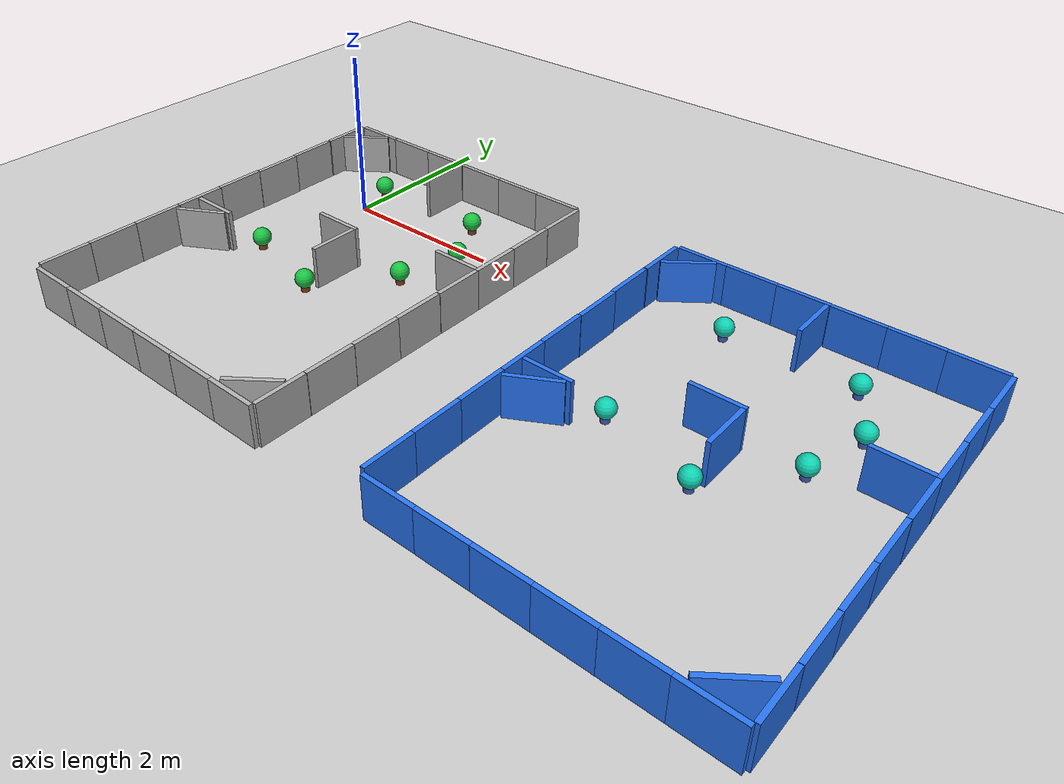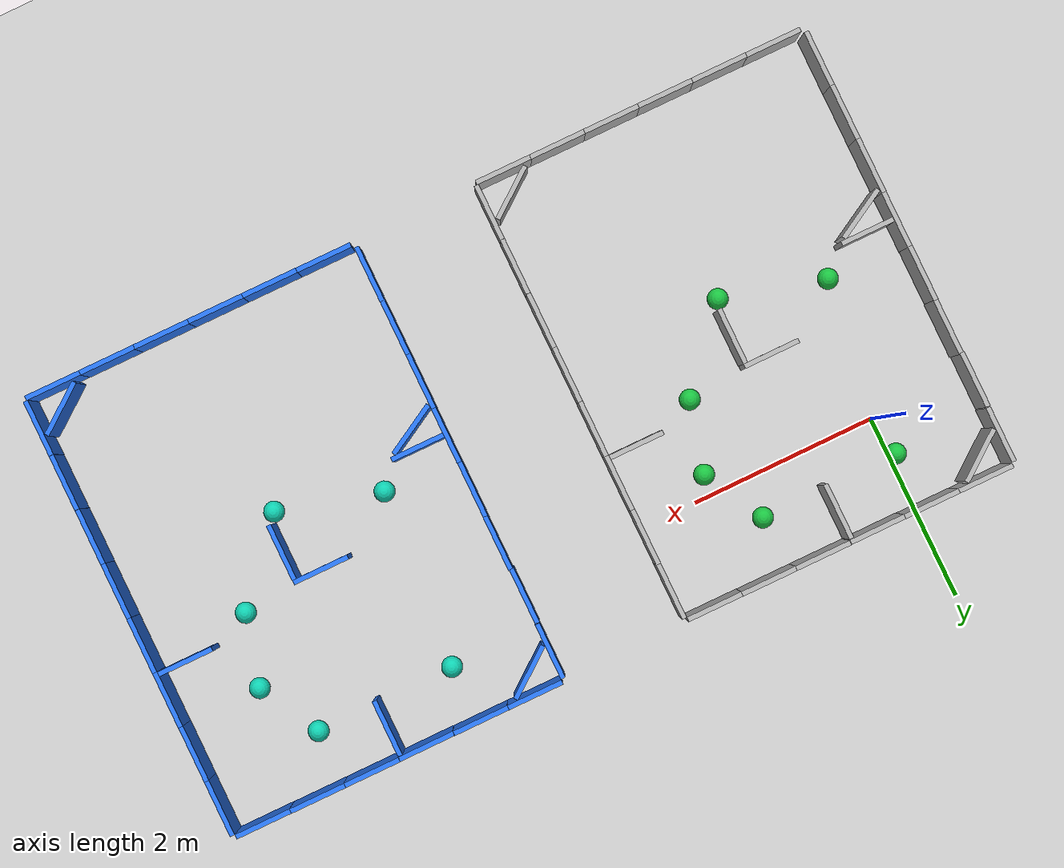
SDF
<?xml version='1.0' encoding='utf-8'?>
<sdf version="1.8">
  <world name="default">
    <physics type="ode">
      <real_time_update_rate>1000.0</real_time_update_rate>
      <max_step_size>0.001</max_step_size>
      <real_time_factor>1</real_time_factor>
      <ode>
        <solver>
          <type>quick</type>
          <iters>150</iters>
          <precon_iters>0</precon_iters>
          <sor>1.400000</sor>
          <use_dynamic_moi_rescaling>1</use_dynamic_moi_rescaling>
        </solver>
        <constraints>
          <cfm>0.00001</cfm>
          <erp>0.2</erp>
          <contact_max_correcting_vel>2000.000000</contact_max_correcting_vel>
          <contact_surface_layer>0.01000</contact_surface_layer>
        </constraints>
      </ode>
    </physics>
    <plugin filename="gz-sim-physics-system" name="gz::sim::systems::Physics">
    </plugin>
    <plugin filename="gz-sim-user-commands-system" name="gz::sim::systems::UserCommands">
    </plugin>
    <plugin filename="gz-sim-scene-broadcaster-system" name="gz::sim::systems::SceneBroadcaster">
    </plugin>
    <plugin filename="gz-sim-sensors-system" name="gz::sim::systems::Sensors">
      <render_engine>ogre2</render_engine>
    </plugin>
    <plugin filename="gz-sim-imu-system" name="gz::sim::systems::Imu">
    </plugin>
    <gravity>0 0 -9.8000000000000007</gravity>
    <magnetic_field>5.5644999999999998e-06 2.2875799999999999e-05 -4.2388400000000002e-05</magnetic_field>
    <atmosphere type="adiabatic" />
    <scene>
      <ambient>0.400000006 0.400000006 0.400000006 1</ambient>
      <background>0.699999988 0.699999988 0.699999988 1</background>
      <shadows>true</shadows>
    </scene>
    <model name="ground_plane">
      <static>true</static>
      <link name="link">
        <collision name="collision">
          <geometry>
            <plane>
              <normal>0 0 1</normal>
              <size>100 100</size>
            </plane>
          </geometry>
          <surface>
            <friction>
              <ode />
            </friction>
            <bounce />
            <contact />
          </surface>
        </collision>
        <visual name="visual">
          <geometry>
            <plane>
              <normal>0 0 1</normal>
              <size>100 100</size>
            </plane>
          </geometry>
          <material>
            <ambient>0.800000012 0.800000012 0.800000012 1</ambient>
            <diffuse>0.800000012 0.800000012 0.800000012 1</diffuse>
            <specular>0.800000012 0.800000012 0.800000012 1</specular>
          </material>
        </visual>
        <pose>0 0 0 0 0 0</pose>
        <inertial>
          <pose>0 0 0 0 0 0</pose>
          <mass>1</mass>
          <inertia>
            <ixx>1</ixx>
            <ixy>0</ixy>
            <ixz>0</ixz>
            <iyy>1</iyy>
            <iyz>0</iyz>
            <izz>1</izz>
          </inertia>
        </inertial>
        <enable_wind>false</enable_wind>
      </link>
      <pose>0 0 0 0 0 0</pose>
      <self_collide>false</self_collide>
    </model>
    <model name="box">
      <pose>-1.0242099761962891 0.67777901887893677 0.26292604207992554 0 0 0</pose>
      <link name="box_link">
        <inertial>
          <inertia>
            <ixx>0.16666</ixx>
            <ixy>0</ixy>
            <ixz>0</ixz>
            <iyy>0.16666</iyy>
            <iyz>0</iyz>
            <izz>0.16666</izz>
          </inertia>
          <mass>1</mass>
          <pose>0 0 0 0 0 0</pose>
        </inertial>
        <collision name="box_collision">
          <geometry>
            <box>
              <size>0.050000000000000003 0.55 0.5</size>
            </box>
          </geometry>
          <surface>
            <friction>
              <ode />
            </friction>
            <bounce />
            <contact />
          </surface>
        </collision>
        <visual name="box_visual">
          <geometry>
            <box>
              <size>0.050000000000000003 0.59999999999999998 0.5</size>
            </box>
          </geometry>
          <material>
            <ambient>0.300000012 0.300000012 0.300000012 1</ambient>
            <diffuse>0.699999988 0.699999988 0.699999988 1</diffuse>
            <specular>1 1 1 1</specular>
          </material>
        </visual>
        <pose>0 0 0 0 0 0</pose>
        <enable_wind>false</enable_wind>
      </link>
      <static>true</static>
      <self_collide>false</self_collide>
    </model>
    <model name="box_1">
      <pose>-1.03 0.070000000000000007 0.26000000000000001 0 0 0</pose>
      <link name="box_link">
        <inertial>
          <inertia>
            <ixx>0.16666</ixx>
            <ixy>0</ixy>
            <ixz>0</ixz>
            <iyy>0.16666</iyy>
            <iyz>0</iyz>
            <izz>0.16666</izz>
          </inertia>
          <mass>1</mass>
          <pose>0 0 0 0 0 0</pose>
        </inertial>
        <collision name="box_collision">
          <geometry>
            <box>
              <size>0.050000000000000003 0.55 0.5</size>
            </box>
          </geometry>
          <surface>
            <friction>
              <ode />
            </friction>
            <bounce />
            <contact />
          </surface>
        </collision>
        <visual name="box_visual">
          <geometry>
            <box>
              <size>0.050000000000000003 0.59999999999999998 0.5</size>
            </box>
          </geometry>
          <material>
            <ambient>0.300000012 0.300000012 0.300000012 1</ambient>
            <diffuse>0.699999988 0.699999988 0.699999988 1</diffuse>
            <specular>1 1 1 1</specular>
          </material>
        </visual>
        <pose>0 0 0 0 0 0</pose>
        <enable_wind>false</enable_wind>
      </link>
      <static>true</static>
      <self_collide>false</self_collide>
    </model>
    <model name="box_2">
      <pose>-1.02 -0.52000000000000002 0.26000000000000001 0 0 0</pose>
      <link name="box_link">
        <inertial>
          <inertia>
            <ixx>0.16666</ixx>
            <ixy>0</ixy>
            <ixz>0</ixz>
            <iyy>0.16666</iyy>
            <iyz>0</iyz>
            <izz>0.16666</izz>
          </inertia>
          <mass>1</mass>
          <pose>0 0 0 0 0 0</pose>
        </inertial>
        <collision name="box_collision">
          <geometry>
            <box>
              <size>0.050000000000000003 0.55 0.5</size>
            </box>
          </geometry>
          <surface>
            <friction>
              <ode />
            </friction>
            <bounce />
            <contact />
          </surface>
        </collision>
        <visual name="box_visual">
          <geometry>
            <box>
              <size>0.050000000000000003 0.59999999999999998 0.5</size>
            </box>
          </geometry>
          <material>
            <ambient>0.300000012 0.300000012 0.300000012 1</ambient>
            <diffuse>0.699999988 0.699999988 0.699999988 1</diffuse>
            <specular>1 1 1 1</specular>
          </material>
        </visual>
        <pose>0 0 0 0 0 0</pose>
        <enable_wind>false</enable_wind>
      </link>
      <static>true</static>
      <self_collide>false</self_collide>
    </model>
    <model name="box_3">
      <pose>-1.0226199626922607 -1.1138999462127686 0.26708531379699707 0 0 0</pose>
      <link name="box_link">
        <inertial>
          <inertia>
            <ixx>0.16666</ixx>
            <ixy>0</ixy>
            <ixz>0</ixz>
            <iyy>0.16666</iyy>
            <iyz>0</iyz>
            <izz>0.16666</izz>
          </inertia>
          <mass>1</mass>
          <pose>0 0 0 0 0 0</pose>
        </inertial>
        <collision name="box_collision">
          <geometry>
            <box>
              <size>0.050000000000000003 0.55 0.5</size>
            </box>
          </geometry>
          <surface>
            <friction>
              <ode />
            </friction>
            <bounce />
            <contact />
          </surface>
        </collision>
        <visual name="box_visual">
          <geometry>
            <box>
              <size>0.050000000000000003 0.59999999999999998 0.5</size>
            </box>
          </geometry>
          <material>
            <ambient>0.300000012 0.300000012 0.300000012 1</ambient>
            <diffuse>0.699999988 0.699999988 0.699999988 1</diffuse>
            <specular>1 1 1 1</specular>
          </material>
        </visual>
        <pose>0 0 0 0 0 0</pose>
        <enable_wind>false</enable_wind>
      </link>
      <static>true</static>
      <self_collide>false</self_collide>
    </model>
    <model name="box_4">
      <pose>-1.0205800533294678 -1.7115800380706787 0.26702764630317688 0 0 0</pose>
      <link name="box_link">
        <inertial>
          <inertia>
            <ixx>0.16666</ixx>
            <ixy>0</ixy>
            <ixz>0</ixz>
            <iyy>0.16666</iyy>
            <iyz>0</iyz>
            <izz>0.16666</izz>
          </inertia>
          <mass>1</mass>
          <pose>0 0 0 0 0 0</pose>
        </inertial>
        <collision name="box_collision">
          <geometry>
            <box>
              <size>0.050000000000000003 0.55 0.5</size>
            </box>
          </geometry>
          <surface>
            <friction>
              <ode />
            </friction>
            <bounce />
            <contact />
          </surface>
        </collision>
        <visual name="box_visual">
          <geometry>
            <box>
              <size>0.050000000000000003 0.59999999999999998 0.5</size>
            </box>
          </geometry>
          <material>
            <ambient>0.300000012 0.300000012 0.300000012 1</ambient>
            <diffuse>0.699999988 0.699999988 0.699999988 1</diffuse>
            <specular>1 1 1 1</specular>
          </material>
        </visual>
        <pose>0 0 0 0 0 0</pose>
        <enable_wind>false</enable_wind>
      </link>
      <static>true</static>
      <self_collide>false</self_collide>
    </model>
    <model name="box_5">
      <pose>-1.023419976234436 -2.3114299774169922 0.26691371202468872 0 0 0</pose>
      <link name="box_link">
        <inertial>
          <inertia>
            <ixx>0.16666</ixx>
            <ixy>0</ixy>
            <ixz>0</ixz>
            <iyy>0.16666</iyy>
            <iyz>0</iyz>
            <izz>0.16666</izz>
          </inertia>
          <mass>1</mass>
          <pose>0 0 0 0 0 0</pose>
        </inertial>
        <collision name="box_collision">
          <geometry>
            <box>
              <size>0.050000000000000003 0.55 0.5</size>
            </box>
          </geometry>
          <surface>
            <friction>
              <ode />
            </friction>
            <bounce />
            <contact />
          </surface>
        </collision>
        <visual name="box_visual">
          <geometry>
            <box>
              <size>0.050000000000000003 0.59999999999999998 0.5</size>
            </box>
          </geometry>
          <material>
            <ambient>0.300000012 0.300000012 0.300000012 1</ambient>
            <diffuse>0.699999988 0.699999988 0.699999988 1</diffuse>
            <specular>1 1 1 1</specular>
          </material>
        </visual>
        <pose>0 0 0 0 0 0</pose>
        <enable_wind>false</enable_wind>
      </link>
      <static>true</static>
      <self_collide>false</self_collide>
    </model>
    <model name="box_6">
      <pose>-1.0233800411224365 -2.9101500511169434 0.26712024211883545 0 0 0</pose>
      <link name="box_link">
        <inertial>
          <inertia>
            <ixx>0.16666</ixx>
            <ixy>0</ixy>
            <ixz>0</ixz>
            <iyy>0.16666</iyy>
            <iyz>0</iyz>
            <izz>0.16666</izz>
          </inertia>
          <mass>1</mass>
          <pose>0 0 0 0 0 0</pose>
        </inertial>
        <collision name="box_collision">
          <geometry>
            <box>
              <size>0.050000000000000003 0.55 0.5</size>
            </box>
          </geometry>
          <surface>
            <friction>
              <ode />
            </friction>
            <bounce />
            <contact />
          </surface>
        </collision>
        <visual name="box_visual">
          <geometry>
            <box>
              <size>0.050000000000000003 0.59999999999999998 0.5</size>
            </box>
          </geometry>
          <material>
            <ambient>0.300000012 0.300000012 0.300000012 1</ambient>
            <diffuse>0.699999988 0.699999988 0.699999988 1</diffuse>
            <specular>1 1 1 1</specular>
          </material>
        </visual>
        <pose>0 0 0 0 0 0</pose>
        <enable_wind>false</enable_wind>
      </link>
      <static>true</static>
      <self_collide>false</self_collide>
    </model>
    <model name="box_7">
      <pose>-1.0221500396728516 -3.5036098957061768 0.26729947328567505 0 0 0</pose>
      <link name="box_link">
        <inertial>
          <inertia>
            <ixx>0.16666</ixx>
            <ixy>0</ixy>
            <ixz>0</ixz>
            <iyy>0.16666</iyy>
            <iyz>0</iyz>
            <izz>0.16666</izz>
          </inertia>
          <mass>1</mass>
          <pose>0 0 0 0 0 0</pose>
        </inertial>
        <collision name="box_collision">
          <geometry>
            <box>
              <size>0.050000000000000003 0.55 0.5</size>
            </box>
          </geometry>
          <surface>
            <friction>
              <ode />
            </friction>
            <bounce />
            <contact />
          </surface>
        </collision>
        <visual name="box_visual">
          <geometry>
            <box>
              <size>0.050000000000000003 0.59999999999999998 0.5</size>
            </box>
          </geometry>
          <material>
            <ambient>0.300000012 0.300000012 0.300000012 1</ambient>
            <diffuse>0.699999988 0.699999988 0.699999988 1</diffuse>
            <specular>1 1 1 1</specular>
          </material>
        </visual>
        <pose>0 0 0 0 0 0</pose>
        <enable_wind>false</enable_wind>
      </link>
      <static>true</static>
      <self_collide>false</self_collide>
    </model>
    <model name="box_8">
      <pose>-0.69749999046325684 1.0066399574279787 0.25750440359115601 0 0 1.5658000872875657</pose>
      <link name="box_link">
        <inertial>
          <inertia>
            <ixx>0.16666</ixx>
            <ixy>0</ixy>
            <ixz>0</ixz>
            <iyy>0.16666</iyy>
            <iyz>0</iyz>
            <izz>0.16666</izz>
          </inertia>
          <mass>1</mass>
          <pose>0 0 0 0 0 0</pose>
        </inertial>
        <collision name="box_collision">
          <geometry>
            <box>
              <size>0.050000000000000003 0.55 0.5</size>
            </box>
          </geometry>
          <surface>
            <friction>
              <ode />
            </friction>
            <bounce />
            <contact />
          </surface>
        </collision>
        <visual name="box_visual">
          <geometry>
            <box>
              <size>0.050000000000000003 0.59999999999999998 0.5</size>
            </box>
          </geometry>
          <material>
            <ambient>0.300000012 0.300000012 0.300000012 1</ambient>
            <diffuse>0.699999988 0.699999988 0.699999988 1</diffuse>
            <specular>1 1 1 1</specular>
          </material>
        </visual>
        <pose>0 0 0 0 0 0</pose>
        <enable_wind>false</enable_wind>
      </link>
      <static>true</static>
      <self_collide>false</self_collide>
    </model>
    <model name="box_8_1">
      <pose>-0.10089799761772156 1.0029499530792234 0.26086625456809998 0 0 1.56841005300998</pose>
      <link name="box_link">
        <inertial>
          <inertia>
            <ixx>0.16666</ixx>
            <ixy>0</ixy>
            <ixz>0</ixz>
            <iyy>0.16666</iyy>
            <iyz>0</iyz>
            <izz>0.16666</izz>
          </inertia>
          <mass>1</mass>
          <pose>0 0 0 0 0 0</pose>
        </inertial>
        <collision name="box_collision">
          <geometry>
            <box>
              <size>0.050000000000000003 0.55 0.5</size>
            </box>
          </geometry>
          <surface>
            <friction>
              <ode />
            </friction>
            <bounce />
            <contact />
          </surface>
        </collision>
        <visual name="box_visual">
          <geometry>
            <box>
              <size>0.050000000000000003 0.59999999999999998 0.5</size>
            </box>
          </geometry>
          <material>
            <ambient>0.300000012 0.300000012 0.300000012 1</ambient>
            <diffuse>0.699999988 0.699999988 0.699999988 1</diffuse>
            <specular>1 1 1 1</specular>
          </material>
        </visual>
        <pose>0 0 0 0 0 0</pose>
        <enable_wind>false</enable_wind>
      </link>
      <static>true</static>
      <self_collide>false</self_collide>
    </model>
    <model name="box_8_2">
      <pose>0.4999748468399049 0.99842858314514138 0.2626970112323761 0 0 1.5700000841906609</pose>
      <link name="box_link">
        <inertial>
          <inertia>
            <ixx>0.16666</ixx>
            <ixy>0</ixy>
            <ixz>0</ixz>
            <iyy>0.16666</iyy>
            <iyz>0</iyz>
            <izz>0.16666</izz>
          </inertia>
          <mass>1</mass>
          <pose>0 0 0 0 0 0</pose>
        </inertial>
        <collision name="box_collision">
          <geometry>
            <box>
              <size>0.050000000000000003 0.55 0.5</size>
            </box>
          </geometry>
          <surface>
            <friction>
              <ode />
            </friction>
            <bounce />
            <contact />
          </surface>
        </collision>
        <visual name="box_visual">
          <geometry>
            <box>
              <size>0.050000000000000003 0.59999999999999998 0.5</size>
            </box>
          </geometry>
          <material>
            <ambient>0.300000012 0.300000012 0.300000012 1</ambient>
            <diffuse>0.699999988 0.699999988 0.699999988 1</diffuse>
            <specular>1 1 1 1</specular>
          </material>
        </visual>
        <pose>0 0 0 0 0 0</pose>
        <enable_wind>false</enable_wind>
      </link>
      <static>true</static>
      <self_collide>false</self_collide>
    </model>
    <model name="box_8_3">
      <pose>1.1022270375607515 0.99910312174961913 0.25750398635864258 0 0 1.5658000872875657</pose>
      <link name="box_link">
        <inertial>
          <inertia>
            <ixx>0.16666</ixx>
            <ixy>0</ixy>
            <ixz>0</ixz>
            <iyy>0.16666</iyy>
            <iyz>0</iyz>
            <izz>0.16666</izz>
          </inertia>
          <mass>1</mass>
          <pose>0 0 0 0 0 0</pose>
        </inertial>
        <collision name="box_collision">
          <geometry>
            <box>
              <size>0.050000000000000003 0.55 0.5</size>
            </box>
          </geometry>
          <surface>
            <friction>
              <ode />
            </friction>
            <bounce />
            <contact />
          </surface>
        </collision>
        <visual name="box_visual">
          <geometry>
            <box>
              <size>0.050000000000000003 0.59999999999999998 0.5</size>
            </box>
          </geometry>
          <material>
            <ambient>0.300000012 0.300000012 0.300000012 1</ambient>
            <diffuse>0.699999988 0.699999988 0.699999988 1</diffuse>
            <specular>1 1 1 1</specular>
          </material>
        </visual>
        <pose>0 0 0 0 0 0</pose>
        <enable_wind>false</enable_wind>
      </link>
      <static>true</static>
      <self_collide>false</self_collide>
    </model>
    <model name="box_8_4">
      <pose>1.701962914249203 0.99650460313267275 0.25750398635864258 0 0 1.5658000872875657</pose>
      <link name="box_link">
        <inertial>
          <inertia>
            <ixx>0.16666</ixx>
            <ixy>0</ixy>
            <ixz>0</ixz>
            <iyy>0.16666</iyy>
            <iyz>0</iyz>
            <izz>0.16666</izz>
          </inertia>
          <mass>1</mass>
          <pose>0 0 0 0 0 0</pose>
        </inertial>
        <collision name="box_collision">
          <geometry>
            <box>
              <size>0.050000000000000003 0.55 0.5</size>
            </box>
          </geometry>
          <surface>
            <friction>
              <ode />
            </friction>
            <bounce />
            <contact />
          </surface>
        </collision>
        <visual name="box_visual">
          <geometry>
            <box>
              <size>0.050000000000000003 0.59999999999999998 0.5</size>
            </box>
          </geometry>
          <material>
            <ambient>0.300000012 0.300000012 0.300000012 1</ambient>
            <diffuse>0.699999988 0.699999988 0.699999988 1</diffuse>
            <specular>1 1 1 1</specular>
          </material>
        </visual>
        <pose>0 0 0 0 0 0</pose>
        <enable_wind>false</enable_wind>
      </link>
      <static>true</static>
      <self_collide>false</self_collide>
    </model>
    <model name="box_8_5">
      <pose>2.3000763394988408 0.99137905356510148 0.25750398635864258 0 0 1.5658000872875657</pose>
      <link name="box_link">
        <inertial>
          <inertia>
            <ixx>0.16666</ixx>
            <ixy>0</ixy>
            <ixz>0</ixz>
            <iyy>0.16666</iyy>
            <iyz>0</iyz>
            <izz>0.16666</izz>
          </inertia>
          <mass>1</mass>
          <pose>0 0 0 0 0 0</pose>
        </inertial>
        <collision name="box_collision">
          <geometry>
            <box>
              <size>0.050000000000000003 0.55 0.5</size>
            </box>
          </geometry>
          <surface>
            <friction>
              <ode />
            </friction>
            <bounce />
            <contact />
          </surface>
        </collision>
        <visual name="box_visual">
          <geometry>
            <box>
              <size>0.050000000000000003 0.59999999999999998 0.5</size>
            </box>
          </geometry>
          <material>
            <ambient>0.300000012 0.300000012 0.300000012 1</ambient>
            <diffuse>0.699999988 0.699999988 0.699999988 1</diffuse>
            <specular>1 1 1 1</specular>
          </material>
        </visual>
        <pose>0 0 0 0 0 0</pose>
        <enable_wind>false</enable_wind>
      </link>
      <static>true</static>
      <self_collide>false</self_collide>
    </model>
    <model name="box_9">
      <pose>2.626252963941734 0.66552933060747566 0.26292601227760315 0 0 0</pose>
      <link name="box_link">
        <inertial>
          <inertia>
            <ixx>0.16666</ixx>
            <ixy>0</ixy>
            <ixz>0</ixz>
            <iyy>0.16666</iyy>
            <iyz>0</iyz>
            <izz>0.16666</izz>
          </inertia>
          <mass>1</mass>
          <pose>0 0 0 0 0 0</pose>
        </inertial>
        <collision name="box_collision">
          <geometry>
            <box>
              <size>0.050000000000000003 0.55 0.5</size>
            </box>
          </geometry>
          <surface>
            <friction>
              <ode />
            </friction>
            <bounce />
            <contact />
          </surface>
        </collision>
        <visual name="box_visual">
          <geometry>
            <box>
              <size>0.050000000000000003 0.59999999999999998 0.5</size>
            </box>
          </geometry>
          <material>
            <ambient>0.300000012 0.300000012 0.300000012 1</ambient>
            <diffuse>0.699999988 0.699999988 0.699999988 1</diffuse>
            <specular>1 1 1 1</specular>
          </material>
        </visual>
        <pose>0 0 0 0 0 0</pose>
        <enable_wind>false</enable_wind>
      </link>
      <static>true</static>
      <self_collide>false</self_collide>
    </model>
    <model name="box_10">
      <pose>2.625702667551475 0.065195542834084463 0.26292601227760315 0 0 0</pose>
      <link name="box_link">
        <inertial>
          <inertia>
            <ixx>0.16666</ixx>
            <ixy>0</ixy>
            <ixz>0</ixz>
            <iyy>0.16666</iyy>
            <iyz>0</iyz>
            <izz>0.16666</izz>
          </inertia>
          <mass>1</mass>
          <pose>0 0 0 0 0 0</pose>
        </inertial>
        <collision name="box_collision">
          <geometry>
            <box>
              <size>0.050000000000000003 0.55 0.5</size>
            </box>
          </geometry>
          <surface>
            <friction>
              <ode />
            </friction>
            <bounce />
            <contact />
          </surface>
        </collision>
        <visual name="box_visual">
          <geometry>
            <box>
              <size>0.050000000000000003 0.59999999999999998 0.5</size>
            </box>
          </geometry>
          <material>
            <ambient>0.300000012 0.300000012 0.300000012 1</ambient>
            <diffuse>0.699999988 0.699999988 0.699999988 1</diffuse>
            <specular>1 1 1 1</specular>
          </material>
        </visual>
        <pose>0 0 0 0 0 0</pose>
        <enable_wind>false</enable_wind>
      </link>
      <static>true</static>
      <self_collide>false</self_collide>
    </model>
    <model name="box_11">
      <pose>2.6275927926499159 -0.53502727789761817 0.26292601227760315 0 0 0</pose>
      <link name="box_link">
        <inertial>
          <inertia>
            <ixx>0.16666</ixx>
            <ixy>0</ixy>
            <ixz>0</ixz>
            <iyy>0.16666</iyy>
            <iyz>0</iyz>
            <izz>0.16666</izz>
          </inertia>
          <mass>1</mass>
          <pose>0 0 0 0 0 0</pose>
        </inertial>
        <collision name="box_collision">
          <geometry>
            <box>
              <size>0.050000000000000003 0.55 0.5</size>
            </box>
          </geometry>
          <surface>
            <friction>
              <ode />
            </friction>
            <bounce />
            <contact />
          </surface>
        </collision>
        <visual name="box_visual">
          <geometry>
            <box>
              <size>0.050000000000000003 0.59999999999999998 0.5</size>
            </box>
          </geometry>
          <material>
            <ambient>0.300000012 0.300000012 0.300000012 1</ambient>
            <diffuse>0.699999988 0.699999988 0.699999988 1</diffuse>
            <specular>1 1 1 1</specular>
          </material>
        </visual>
        <pose>0 0 0 0 0 0</pose>
        <enable_wind>false</enable_wind>
      </link>
      <static>true</static>
      <self_collide>false</self_collide>
    </model>
    <model name="box_12">
      <pose>2.6281152505346235 -1.1352186579326506 0.26292601227760315 0 0 0</pose>
      <link name="box_link">
        <inertial>
          <inertia>
            <ixx>0.16666</ixx>
            <ixy>0</ixy>
            <ixz>0</ixz>
            <iyy>0.16666</iyy>
            <iyz>0</iyz>
            <izz>0.16666</izz>
          </inertia>
          <mass>1</mass>
          <pose>0 0 0 0 0 0</pose>
        </inertial>
        <collision name="box_collision">
          <geometry>
            <box>
              <size>0.050000000000000003 0.55 0.5</size>
            </box>
          </geometry>
          <surface>
            <friction>
              <ode />
            </friction>
            <bounce />
            <contact />
          </surface>
        </collision>
        <visual name="box_visual">
          <geometry>
            <box>
              <size>0.050000000000000003 0.59999999999999998 0.5</size>
            </box>
          </geometry>
          <material>
            <ambient>0.300000012 0.300000012 0.300000012 1</ambient>
            <diffuse>0.699999988 0.699999988 0.699999988 1</diffuse>
            <specular>1 1 1 1</specular>
          </material>
        </visual>
        <pose>0 0 0 0 0 0</pose>
        <enable_wind>false</enable_wind>
      </link>
      <static>true</static>
      <self_collide>false</self_collide>
    </model>
    <model name="box_13">
      <pose>2.6267948704934359 -1.7371728259073804 0.26292601227760315 0 0 0</pose>
      <link name="box_link">
        <inertial>
          <inertia>
            <ixx>0.16666</ixx>
            <ixy>0</ixy>
            <ixz>0</ixz>
            <iyy>0.16666</iyy>
            <iyz>0</iyz>
            <izz>0.16666</izz>
          </inertia>
          <mass>1</mass>
          <pose>0 0 0 0 0 0</pose>
        </inertial>
        <collision name="box_collision">
          <geometry>
            <box>
              <size>0.050000000000000003 0.55 0.5</size>
            </box>
          </geometry>
          <surface>
            <friction>
              <ode />
            </friction>
            <bounce />
            <contact />
          </surface>
        </collision>
        <visual name="box_visual">
          <geometry>
            <box>
              <size>0.050000000000000003 0.59999999999999998 0.5</size>
            </box>
          </geometry>
          <material>
            <ambient>0.300000012 0.300000012 0.300000012 1</ambient>
            <diffuse>0.699999988 0.699999988 0.699999988 1</diffuse>
            <specular>1 1 1 1</specular>
          </material>
        </visual>
        <pose>0 0 0 0 0 0</pose>
        <enable_wind>false</enable_wind>
      </link>
      <static>true</static>
      <self_collide>false</self_collide>
    </model>
    <model name="box_14">
      <pose>2.6267614305352369 -2.3366292042299199 0.26292601227760315 0 0 0</pose>
      <link name="box_link">
        <inertial>
          <inertia>
            <ixx>0.16666</ixx>
            <ixy>0</ixy>
            <ixz>0</ixz>
            <iyy>0.16666</iyy>
            <iyz>0</iyz>
            <izz>0.16666</izz>
          </inertia>
          <mass>1</mass>
          <pose>0 0 0 0 0 0</pose>
        </inertial>
        <collision name="box_collision">
          <geometry>
            <box>
              <size>0.050000000000000003 0.55 0.5</size>
            </box>
          </geometry>
          <surface>
            <friction>
              <ode />
            </friction>
            <bounce />
            <contact />
          </surface>
        </collision>
        <visual name="box_visual">
          <geometry>
            <box>
              <size>0.050000000000000003 0.59999999999999998 0.5</size>
            </box>
          </geometry>
          <material>
            <ambient>0.300000012 0.300000012 0.300000012 1</ambient>
            <diffuse>0.699999988 0.699999988 0.699999988 1</diffuse>
            <specular>1 1 1 1</specular>
          </material>
        </visual>
        <pose>0 0 0 0 0 0</pose>
        <enable_wind>false</enable_wind>
      </link>
      <static>true</static>
      <self_collide>false</self_collide>
    </model>
    <model name="box_15">
      <pose>2.6280006269886167 -2.9389073220340531 0.26292601227760315 0 0 0</pose>
      <link name="box_link">
        <inertial>
          <inertia>
            <ixx>0.16666</ixx>
            <ixy>0</ixy>
            <ixz>0</ixz>
            <iyy>0.16666</iyy>
            <iyz>0</iyz>
            <izz>0.16666</izz>
          </inertia>
          <mass>1</mass>
          <pose>0 0 0 0 0 0</pose>
        </inertial>
        <collision name="box_collision">
          <geometry>
            <box>
              <size>0.050000000000000003 0.55 0.5</size>
            </box>
          </geometry>
          <surface>
            <friction>
              <ode />
            </friction>
            <bounce />
            <contact />
          </surface>
        </collision>
        <visual name="box_visual">
          <geometry>
            <box>
              <size>0.050000000000000003 0.59999999999999998 0.5</size>
            </box>
          </geometry>
          <material>
            <ambient>0.300000012 0.300000012 0.300000012 1</ambient>
            <diffuse>0.699999988 0.699999988 0.699999988 1</diffuse>
            <specular>1 1 1 1</specular>
          </material>
        </visual>
        <pose>0 0 0 0 0 0</pose>
        <enable_wind>false</enable_wind>
      </link>
      <static>true</static>
      <self_collide>false</self_collide>
    </model>
    <model name="box_16">
      <pose>2.6274764676781759 -3.5421945732274764 0.26292601227760315 0 0 0</pose>
      <link name="box_link">
        <inertial>
          <inertia>
            <ixx>0.16666</ixx>
            <ixy>0</ixy>
            <ixz>0</ixz>
            <iyy>0.16666</iyy>
            <iyz>0</iyz>
            <izz>0.16666</izz>
          </inertia>
          <mass>1</mass>
          <pose>0 0 0 0 0 0</pose>
        </inertial>
        <collision name="box_collision">
          <geometry>
            <box>
              <size>0.050000000000000003 0.55 0.5</size>
            </box>
          </geometry>
          <surface>
            <friction>
              <ode />
            </friction>
            <bounce />
            <contact />
          </surface>
        </collision>
        <visual name="box_visual">
          <geometry>
            <box>
              <size>0.050000000000000003 0.59999999999999998 0.5</size>
            </box>
          </geometry>
          <material>
            <ambient>0.300000012 0.300000012 0.300000012 1</ambient>
            <diffuse>0.699999988 0.699999988 0.699999988 1</diffuse>
            <specular>1 1 1 1</specular>
          </material>
        </visual>
        <pose>0 0 0 0 0 0</pose>
        <enable_wind>false</enable_wind>
      </link>
      <static>true</static>
      <self_collide>false</self_collide>
    </model>
    <model name="box_8_5_1">
      <pose>2.3170975934162765 -3.8655655792473209 0.25750398635864258 0 0 1.5658000872875657</pose>
      <link name="box_link">
        <inertial>
          <inertia>
            <ixx>0.16666</ixx>
            <ixy>0</ixy>
            <ixz>0</ixz>
            <iyy>0.16666</iyy>
            <iyz>0</iyz>
            <izz>0.16666</izz>
          </inertia>
          <mass>1</mass>
          <pose>0 0 0 0 0 0</pose>
        </inertial>
        <collision name="box_collision">
          <geometry>
            <box>
              <size>0.050000000000000003 0.55 0.5</size>
            </box>
          </geometry>
          <surface>
            <friction>
              <ode />
            </friction>
            <bounce />
            <contact />
          </surface>
        </collision>
        <visual name="box_visual">
          <geometry>
            <box>
              <size>0.050000000000000003 0.59999999999999998 0.5</size>
            </box>
          </geometry>
          <material>
            <ambient>0.300000012 0.300000012 0.300000012 1</ambient>
            <diffuse>0.699999988 0.699999988 0.699999988 1</diffuse>
            <specular>1 1 1 1</specular>
          </material>
        </visual>
        <pose>0 0 0 0 0 0</pose>
        <enable_wind>false</enable_wind>
      </link>
      <static>true</static>
      <self_collide>false</self_collide>
    </model>
    <model name="box_8_5_2">
      <pose>1.7183380653296056 -3.862349183830966 0.25750398635864258 0 0 1.5658000872875657</pose>
      <link name="box_link">
        <inertial>
          <inertia>
            <ixx>0.16666</ixx>
            <ixy>0</ixy>
            <ixz>0</ixz>
            <iyy>0.16666</iyy>
            <iyz>0</iyz>
            <izz>0.16666</izz>
          </inertia>
          <mass>1</mass>
          <pose>0 0 0 0 0 0</pose>
        </inertial>
        <collision name="box_collision">
          <geometry>
            <box>
              <size>0.050000000000000003 0.55 0.5</size>
            </box>
          </geometry>
          <surface>
            <friction>
              <ode />
            </friction>
            <bounce />
            <contact />
          </surface>
        </collision>
        <visual name="box_visual">
          <geometry>
            <box>
              <size>0.050000000000000003 0.59999999999999998 0.5</size>
            </box>
          </geometry>
          <material>
            <ambient>0.300000012 0.300000012 0.300000012 1</ambient>
            <diffuse>0.699999988 0.699999988 0.699999988 1</diffuse>
            <specular>1 1 1 1</specular>
          </material>
        </visual>
        <pose>0 0 0 0 0 0</pose>
        <enable_wind>false</enable_wind>
      </link>
      <static>true</static>
      <self_collide>false</self_collide>
    </model>
    <model name="box_8_5_3">
      <pose>1.1190764522698835 -3.8600206948799998 0.25750398635864258 0 0 1.5658000872875657</pose>
      <link name="box_link">
        <inertial>
          <inertia>
            <ixx>0.16666</ixx>
            <ixy>0</ixy>
            <ixz>0</ixz>
            <iyy>0.16666</iyy>
            <iyz>0</iyz>
            <izz>0.16666</izz>
          </inertia>
          <mass>1</mass>
          <pose>0 0 0 0 0 0</pose>
        </inertial>
        <collision name="box_collision">
          <geometry>
            <box>
              <size>0.050000000000000003 0.55 0.5</size>
            </box>
          </geometry>
          <surface>
            <friction>
              <ode />
            </friction>
            <bounce />
            <contact />
          </surface>
        </collision>
        <visual name="box_visual">
          <geometry>
            <box>
              <size>0.050000000000000003 0.59999999999999998 0.5</size>
            </box>
          </geometry>
          <material>
            <ambient>0.300000012 0.300000012 0.300000012 1</ambient>
            <diffuse>0.699999988 0.699999988 0.699999988 1</diffuse>
            <specular>1 1 1 1</specular>
          </material>
        </visual>
        <pose>0 0 0 0 0 0</pose>
        <enable_wind>false</enable_wind>
      </link>
      <static>true</static>
      <self_collide>false</self_collide>
    </model>
    <model name="box_8_5_4">
      <pose>0.52016775223423839 -3.8568482565905109 0.25750398635864258 0 0 1.5658000872875657</pose>
      <link name="box_link">
        <inertial>
          <inertia>
            <ixx>0.16666</ixx>
            <ixy>0</ixy>
            <ixz>0</ixz>
            <iyy>0.16666</iyy>
            <iyz>0</iyz>
            <izz>0.16666</izz>
          </inertia>
          <mass>1</mass>
          <pose>0 0 0 0 0 0</pose>
        </inertial>
        <collision name="box_collision">
          <geometry>
            <box>
              <size>0.050000000000000003 0.55 0.5</size>
            </box>
          </geometry>
          <surface>
            <friction>
              <ode />
            </friction>
            <bounce />
            <contact />
          </surface>
        </collision>
        <visual name="box_visual">
          <geometry>
            <box>
              <size>0.050000000000000003 0.59999999999999998 0.5</size>
            </box>
          </geometry>
          <material>
            <ambient>0.300000012 0.300000012 0.300000012 1</ambient>
            <diffuse>0.699999988 0.699999988 0.699999988 1</diffuse>
            <specular>1 1 1 1</specular>
          </material>
        </visual>
        <pose>0 0 0 0 0 0</pose>
        <enable_wind>false</enable_wind>
      </link>
      <static>true</static>
      <self_collide>false</self_collide>
    </model>
    <model name="box_8_5_5">
      <pose>-0.080121158882265009 -3.8538894517536315 0.25750398635864258 0 0 1.5658000872875657</pose>
      <link name="box_link">
        <inertial>
          <inertia>
            <ixx>0.16666</ixx>
            <ixy>0</ixy>
            <ixz>0</ixz>
            <iyy>0.16666</iyy>
            <iyz>0</iyz>
            <izz>0.16666</izz>
          </inertia>
          <mass>1</mass>
          <pose>0 0 0 0 0 0</pose>
        </inertial>
        <collision name="box_collision">
          <geometry>
            <box>
              <size>0.050000000000000003 0.55 0.5</size>
            </box>
          </geometry>
          <surface>
            <friction>
              <ode />
            </friction>
            <bounce />
            <contact />
          </surface>
        </collision>
        <visual name="box_visual">
          <geometry>
            <box>
              <size>0.050000000000000003 0.59999999999999998 0.5</size>
            </box>
          </geometry>
          <material>
            <ambient>0.300000012 0.300000012 0.300000012 1</ambient>
            <diffuse>0.699999988 0.699999988 0.699999988 1</diffuse>
            <specular>1 1 1 1</specular>
          </material>
        </visual>
        <pose>0 0 0 0 0 0</pose>
        <enable_wind>false</enable_wind>
      </link>
      <static>true</static>
      <self_collide>false</self_collide>
    </model>
    <model name="box_8_5_6">
      <pose>-0.67984316614260165 -3.8498007437380806 0.25750398635864258 0 0 1.5658000872875657</pose>
      <link name="box_link">
        <inertial>
          <inertia>
            <ixx>0.16666</ixx>
            <ixy>0</ixy>
            <ixz>0</ixz>
            <iyy>0.16666</iyy>
            <iyz>0</iyz>
            <izz>0.16666</izz>
          </inertia>
          <mass>1</mass>
          <pose>0 0 0 0 0 0</pose>
        </inertial>
        <collision name="box_collision">
          <geometry>
            <box>
              <size>0.050000000000000003 0.55 0.5</size>
            </box>
          </geometry>
          <surface>
            <friction>
              <ode />
            </friction>
            <bounce />
            <contact />
          </surface>
        </collision>
        <visual name="box_visual">
          <geometry>
            <box>
              <size>0.050000000000000003 0.59999999999999998 0.5</size>
            </box>
          </geometry>
          <material>
            <ambient>0.300000012 0.300000012 0.300000012 1</ambient>
            <diffuse>0.699999988 0.699999988 0.699999988 1</diffuse>
            <specular>1 1 1 1</specular>
          </material>
        </visual>
        <pose>0 0 0 0 0 0</pose>
        <enable_wind>false</enable_wind>
      </link>
      <static>true</static>
      <self_collide>false</self_collide>
    </model>
    <model name="box_8_5_7">
      <pose>-0.71799231176185963 -1.7295482278429848 0.25750398635864258 0 0 1.5658000872875657</pose>
      <link name="box_link">
        <inertial>
          <inertia>
            <ixx>0.16666</ixx>
            <ixy>0</ixy>
            <ixz>0</ixz>
            <iyy>0.16666</iyy>
            <iyz>0</iyz>
            <izz>0.16666</izz>
          </inertia>
          <mass>1</mass>
          <pose>0 0 0 0 0 0</pose>
        </inertial>
        <collision name="box_collision">
          <geometry>
            <box>
              <size>0.050000000000000003 0.55 0.5</size>
            </box>
          </geometry>
          <surface>
            <friction>
              <ode />
            </friction>
            <bounce />
            <contact />
          </surface>
        </collision>
        <visual name="box_visual">
          <geometry>
            <box>
              <size>0.050000000000000003 0.59999999999999998 0.5</size>
            </box>
          </geometry>
          <material>
            <ambient>0.300000012 0.300000012 0.300000012 1</ambient>
            <diffuse>0.699999988 0.699999988 0.699999988 1</diffuse>
            <specular>1 1 1 1</specular>
          </material>
        </visual>
        <pose>0 0 0 0 0 0</pose>
        <enable_wind>false</enable_wind>
      </link>
      <static>true</static>
      <self_collide>false</self_collide>
    </model>
    <model name="box_8_5_9">
      <pose>2.3106882813119443 -0.80301534855683077 0.25750398635864258 0 0 1.5658000872875657</pose>
      <link name="box_link">
        <inertial>
          <inertia>
            <ixx>0.16666</ixx>
            <ixy>0</ixy>
            <ixz>0</ixz>
            <iyy>0.16666</iyy>
            <iyz>0</iyz>
            <izz>0.16666</izz>
          </inertia>
          <mass>1</mass>
          <pose>0 0 0 0 0 0</pose>
        </inertial>
        <collision name="box_collision">
          <geometry>
            <box>
              <size>0.050000000000000003 0.55 0.5</size>
            </box>
          </geometry>
          <surface>
            <friction>
              <ode />
            </friction>
            <bounce />
            <contact />
          </surface>
        </collision>
        <visual name="box_visual">
          <geometry>
            <box>
              <size>0.050000000000000003 0.59999999999999998 0.5</size>
            </box>
          </geometry>
          <material>
            <ambient>0.300000012 0.300000012 0.300000012 1</ambient>
            <diffuse>0.699999988 0.699999988 0.699999988 1</diffuse>
            <specular>1 1 1 1</specular>
          </material>
        </visual>
        <pose>0 0 0 0 0 0</pose>
        <enable_wind>false</enable_wind>
      </link>
      <static>true</static>
      <self_collide>false</self_collide>
    </model>
    <model name="box_1_1">
      <pose>0.77402352846331013 0.66890409951665486 0.26661500334739685 0 0 0</pose>
      <link name="box_link">
        <inertial>
          <inertia>
            <ixx>0.16666</ixx>
            <ixy>0</ixy>
            <ixz>0</ixz>
            <iyy>0.16666</iyy>
            <iyz>0</iyz>
            <izz>0.16666</izz>
          </inertia>
          <mass>1</mass>
          <pose>0 0 0 0 0 0</pose>
        </inertial>
        <collision name="box_collision">
          <geometry>
            <box>
              <size>0.050000000000000003 0.55 0.5</size>
            </box>
          </geometry>
          <surface>
            <friction>
              <ode />
            </friction>
            <bounce />
            <contact />
          </surface>
        </collision>
        <visual name="box_visual">
          <geometry>
            <box>
              <size>0.050000000000000003 0.59999999999999998 0.5</size>
            </box>
          </geometry>
          <material>
            <ambient>0.300000012 0.300000012 0.300000012 1</ambient>
            <diffuse>0.699999988 0.699999988 0.699999988 1</diffuse>
            <specular>1 1 1 1</specular>
          </material>
        </visual>
        <pose>0 0 0 0 0 0</pose>
        <enable_wind>false</enable_wind>
      </link>
      <static>true</static>
      <self_collide>false</self_collide>
    </model>
    <model name="box_1_2_2">
      <pose>-0.74630128513783545 0.77809146078665803 0.26661500334739685 0 0 -0.9211320022812256</pose>
      <link name="box_link">
        <inertial>
          <inertia>
            <ixx>0.16666</ixx>
            <ixy>0</ixy>
            <ixz>0</ixz>
            <iyy>0.16666</iyy>
            <iyz>0</iyz>
            <izz>0.16666</izz>
          </inertia>
          <mass>1</mass>
          <pose>0 0 0 0 0 0</pose>
        </inertial>
        <collision name="box_collision">
          <geometry>
            <box>
              <size>0.050000000000000003 0.55 0.5</size>
            </box>
          </geometry>
          <surface>
            <friction>
              <ode />
            </friction>
            <bounce />
            <contact />
          </surface>
        </collision>
        <visual name="box_visual">
          <geometry>
            <box>
              <size>0.050000000000000003 0.59999999999999998 0.5</size>
            </box>
          </geometry>
          <material>
            <ambient>0.300000012 0.300000012 0.300000012 1</ambient>
            <diffuse>0.699999988 0.699999988 0.699999988 1</diffuse>
            <specular>1 1 1 1</specular>
          </material>
        </visual>
        <pose>0 0 0 0 0 0</pose>
        <enable_wind>false</enable_wind>
      </link>
      <static>true</static>
      <self_collide>false</self_collide>
    </model>
    <model name="box_1_2_3">
      <pose>2.3426086092275002 -3.6236037284401896 0.26661500334739685 0 0 -0.9211320022812256</pose>
      <link name="box_link">
        <inertial>
          <inertia>
            <ixx>0.16666</ixx>
            <ixy>0</ixy>
            <ixz>0</ixz>
            <iyy>0.16666</iyy>
            <iyz>0</iyz>
            <izz>0.16666</izz>
          </inertia>
          <mass>1</mass>
          <pose>0 0 0 0 0 0</pose>
        </inertial>
        <collision name="box_collision">
          <geometry>
            <box>
              <size>0.050000000000000003 0.55 0.5</size>
            </box>
          </geometry>
          <surface>
            <friction>
              <ode />
            </friction>
            <bounce />
            <contact />
          </surface>
        </collision>
        <visual name="box_visual">
          <geometry>
            <box>
              <size>0.050000000000000003 0.59999999999999998 0.5</size>
            </box>
          </geometry>
          <material>
            <ambient>0.300000012 0.300000012 0.300000012 1</ambient>
            <diffuse>0.699999988 0.699999988 0.699999988 1</diffuse>
            <specular>1 1 1 1</specular>
          </material>
        </visual>
        <pose>0 0 0 0 0 0</pose>
        <enable_wind>false</enable_wind>
      </link>
      <static>true</static>
      <self_collide>false</self_collide>
    </model>
    <model name="box_8_5_8_3">
      <pose>-0.72633250227749258 -1.9181128806837573 0.25750398635864258 0 0 2.0823900577787207</pose>
      <link name="box_link">
        <inertial>
          <inertia>
            <ixx>0.16666</ixx>
            <ixy>0</ixy>
            <ixz>0</ixz>
            <iyy>0.16666</iyy>
            <iyz>0</iyz>
            <izz>0.16666</izz>
          </inertia>
          <mass>1</mass>
          <pose>0 0 0 0 0 0</pose>
        </inertial>
        <collision name="box_collision">
          <geometry>
            <box>
              <size>0.050000000000000003 0.55 0.5</size>
            </box>
          </geometry>
          <surface>
            <friction>
              <ode />
            </friction>
            <bounce />
            <contact />
          </surface>
        </collision>
        <visual name="box_visual">
          <geometry>
            <box>
              <size>0.050000000000000003 0.59999999999999998 0.5</size>
            </box>
          </geometry>
          <material>
            <ambient>0.300000012 0.300000012 0.300000012 1</ambient>
            <diffuse>0.699999988 0.699999988 0.699999988 1</diffuse>
            <specular>1 1 1 1</specular>
          </material>
        </visual>
        <pose>0 0 0 0 0 0</pose>
        <enable_wind>false</enable_wind>
      </link>
      <static>true</static>
      <self_collide>false</self_collide>
    </model>
    <model name="box_1_1_1">
      <pose>0.97109466823778412 -1.3696296970979935 0.26661500334739685 0 0 0</pose>
      <link name="box_link">
        <inertial>
          <inertia>
            <ixx>0.16666</ixx>
            <ixy>0</ixy>
            <ixz>0</ixz>
            <iyy>0.16666</iyy>
            <iyz>0</iyz>
            <izz>0.16666</izz>
          </inertia>
          <mass>1</mass>
          <pose>0 0 0 0 0 0</pose>
        </inertial>
        <collision name="box_collision">
          <geometry>
            <box>
              <size>0.050000000000000003 0.55 0.5</size>
            </box>
          </geometry>
          <surface>
            <friction>
              <ode />
            </friction>
            <bounce />
            <contact />
          </surface>
        </collision>
        <visual name="box_visual">
          <geometry>
            <box>
              <size>0.050000000000000003 0.59999999999999998 0.5</size>
            </box>
          </geometry>
          <material>
            <ambient>0.300000012 0.300000012 0.300000012 1</ambient>
            <diffuse>0.699999988 0.699999988 0.699999988 1</diffuse>
            <specular>1 1 1 1</specular>
          </material>
        </visual>
        <pose>0 0 0 0 0 0</pose>
        <enable_wind>false</enable_wind>
      </link>
      <static>true</static>
      <self_collide>false</self_collide>
    </model>
    <model name="box_8_1_1">
      <pose>0.69148297125501235 -1.0442157666892553 0.26086598634719849 0 0 1.56841005300998</pose>
      <link name="box_link">
        <inertial>
          <inertia>
            <ixx>0.16666</ixx>
            <ixy>0</ixy>
            <ixz>0</ixz>
            <iyy>0.16666</iyy>
            <iyz>0</iyz>
            <izz>0.16666</izz>
          </inertia>
          <mass>1</mass>
          <pose>0 0 0 0 0 0</pose>
        </inertial>
        <collision name="box_collision">
          <geometry>
            <box>
              <size>0.050000000000000003 0.55 0.5</size>
            </box>
          </geometry>
          <surface>
            <friction>
              <ode />
            </friction>
            <bounce />
            <contact />
          </surface>
        </collision>
        <visual name="box_visual">
          <geometry>
            <box>
              <size>0.050000000000000003 0.59999999999999998 0.5</size>
            </box>
          </geometry>
          <material>
            <ambient>0.300000012 0.300000012 0.300000012 1</ambient>
            <diffuse>0.699999988 0.699999988 0.699999988 1</diffuse>
            <specular>1 1 1 1</specular>
          </material>
        </visual>
        <pose>0 0 0 0 0 0</pose>
        <enable_wind>false</enable_wind>
      </link>
      <static>true</static>
      <self_collide>false</self_collide>
    </model>
    <model name="digital_box">
      <pose>3.9757900238 0.67777901887893677 0.26292604207992554 0 0 0</pose>
      <link name="box_link">
        <inertial>
          <inertia>
            <ixx>0.16666</ixx>
            <ixy>0</ixy>
            <ixz>0</ixz>
            <iyy>0.16666</iyy>
            <iyz>0</iyz>
            <izz>0.16666</izz>
          </inertia>
          <mass>1</mass>
          <pose>0 0 0 0 0 0</pose>
        </inertial>
        <collision name="box_collision">
          <geometry>
            <box>
              <size>0.050000000000000003 0.55 0.5</size>
            </box>
          </geometry>
          <surface>
            <friction>
              <ode />
            </friction>
            <bounce />
            <contact />
          </surface>
        </collision>
        <visual name="box_visual">
          <geometry>
            <box>
              <size>0.050000000000000003 0.59999999999999998 0.5</size>
            </box>
          </geometry>
          <material>
            <ambient>0.08 0.28 0.75 1</ambient>
            <diffuse>0.16 0.46 0.95 1</diffuse>
            <specular>1 1 1 1</specular>
          </material>
        </visual>
        <pose>0 0 0 0 0 0</pose>
        <enable_wind>false</enable_wind>
      </link>
      <static>true</static>
      <self_collide>false</self_collide>
    </model>
    <model name="digital_box_1">
      <pose>3.97 0.070000000000000007 0.26000000000000001 0 0 0</pose>
      <link name="box_link">
        <inertial>
          <inertia>
            <ixx>0.16666</ixx>
            <ixy>0</ixy>
            <ixz>0</ixz>
            <iyy>0.16666</iyy>
            <iyz>0</iyz>
            <izz>0.16666</izz>
          </inertia>
          <mass>1</mass>
          <pose>0 0 0 0 0 0</pose>
        </inertial>
        <collision name="box_collision">
          <geometry>
            <box>
              <size>0.050000000000000003 0.55 0.5</size>
            </box>
          </geometry>
          <surface>
            <friction>
              <ode />
            </friction>
            <bounce />
            <contact />
          </surface>
        </collision>
        <visual name="box_visual">
          <geometry>
            <box>
              <size>0.050000000000000003 0.59999999999999998 0.5</size>
            </box>
          </geometry>
          <material>
            <ambient>0.08 0.28 0.75 1</ambient>
            <diffuse>0.16 0.46 0.95 1</diffuse>
            <specular>1 1 1 1</specular>
          </material>
        </visual>
        <pose>0 0 0 0 0 0</pose>
        <enable_wind>false</enable_wind>
      </link>
      <static>true</static>
      <self_collide>false</self_collide>
    </model>
    <model name="digital_box_2">
      <pose>3.98 -0.52000000000000002 0.26000000000000001 0 0 0</pose>
      <link name="box_link">
        <inertial>
          <inertia>
            <ixx>0.16666</ixx>
            <ixy>0</ixy>
            <ixz>0</ixz>
            <iyy>0.16666</iyy>
            <iyz>0</iyz>
            <izz>0.16666</izz>
          </inertia>
          <mass>1</mass>
          <pose>0 0 0 0 0 0</pose>
        </inertial>
        <collision name="box_collision">
          <geometry>
            <box>
              <size>0.050000000000000003 0.55 0.5</size>
            </box>
          </geometry>
          <surface>
            <friction>
              <ode />
            </friction>
            <bounce />
            <contact />
          </surface>
        </collision>
        <visual name="box_visual">
          <geometry>
            <box>
              <size>0.050000000000000003 0.59999999999999998 0.5</size>
            </box>
          </geometry>
          <material>
            <ambient>0.08 0.28 0.75 1</ambient>
            <diffuse>0.16 0.46 0.95 1</diffuse>
            <specular>1 1 1 1</specular>
          </material>
        </visual>
        <pose>0 0 0 0 0 0</pose>
        <enable_wind>false</enable_wind>
      </link>
      <static>true</static>
      <self_collide>false</self_collide>
    </model>
    <model name="digital_box_3">
      <pose>3.97738003731 -1.1138999462127686 0.26708531379699707 0 0 0</pose>
      <link name="box_link">
        <inertial>
          <inertia>
            <ixx>0.16666</ixx>
            <ixy>0</ixy>
            <ixz>0</ixz>
            <iyy>0.16666</iyy>
            <iyz>0</iyz>
            <izz>0.16666</izz>
          </inertia>
          <mass>1</mass>
          <pose>0 0 0 0 0 0</pose>
        </inertial>
        <collision name="box_collision">
          <geometry>
            <box>
              <size>0.050000000000000003 0.55 0.5</size>
            </box>
          </geometry>
          <surface>
            <friction>
              <ode />
            </friction>
            <bounce />
            <contact />
          </surface>
        </collision>
        <visual name="box_visual">
          <geometry>
            <box>
              <size>0.050000000000000003 0.59999999999999998 0.5</size>
            </box>
          </geometry>
          <material>
            <ambient>0.08 0.28 0.75 1</ambient>
            <diffuse>0.16 0.46 0.95 1</diffuse>
            <specular>1 1 1 1</specular>
          </material>
        </visual>
        <pose>0 0 0 0 0 0</pose>
        <enable_wind>false</enable_wind>
      </link>
      <static>true</static>
      <self_collide>false</self_collide>
    </model>
    <model name="digital_box_4">
      <pose>3.97941994667 -1.7115800380706787 0.26702764630317688 0 0 0</pose>
      <link name="box_link">
        <inertial>
          <inertia>
            <ixx>0.16666</ixx>
            <ixy>0</ixy>
            <ixz>0</ixz>
            <iyy>0.16666</iyy>
            <iyz>0</iyz>
            <izz>0.16666</izz>
          </inertia>
          <mass>1</mass>
          <pose>0 0 0 0 0 0</pose>
        </inertial>
        <collision name="box_collision">
          <geometry>
            <box>
              <size>0.050000000000000003 0.55 0.5</size>
            </box>
          </geometry>
          <surface>
            <friction>
              <ode />
            </friction>
            <bounce />
            <contact />
          </surface>
        </collision>
        <visual name="box_visual">
          <geometry>
            <box>
              <size>0.050000000000000003 0.59999999999999998 0.5</size>
            </box>
          </geometry>
          <material>
            <ambient>0.08 0.28 0.75 1</ambient>
            <diffuse>0.16 0.46 0.95 1</diffuse>
            <specular>1 1 1 1</specular>
          </material>
        </visual>
        <pose>0 0 0 0 0 0</pose>
        <enable_wind>false</enable_wind>
      </link>
      <static>true</static>
      <self_collide>false</self_collide>
    </model>
    <model name="digital_box_5">
      <pose>3.97658002377 -2.3114299774169922 0.26691371202468872 0 0 0</pose>
      <link name="box_link">
        <inertial>
          <inertia>
            <ixx>0.16666</ixx>
            <ixy>0</ixy>
            <ixz>0</ixz>
            <iyy>0.16666</iyy>
            <iyz>0</iyz>
            <izz>0.16666</izz>
          </inertia>
          <mass>1</mass>
          <pose>0 0 0 0 0 0</pose>
        </inertial>
        <collision name="box_collision">
          <geometry>
            <box>
              <size>0.050000000000000003 0.55 0.5</size>
            </box>
          </geometry>
          <surface>
            <friction>
              <ode />
            </friction>
            <bounce />
            <contact />
          </surface>
        </collision>
        <visual name="box_visual">
          <geometry>
            <box>
              <size>0.050000000000000003 0.59999999999999998 0.5</size>
            </box>
          </geometry>
          <material>
            <ambient>0.08 0.28 0.75 1</ambient>
            <diffuse>0.16 0.46 0.95 1</diffuse>
            <specular>1 1 1 1</specular>
          </material>
        </visual>
        <pose>0 0 0 0 0 0</pose>
        <enable_wind>false</enable_wind>
      </link>
      <static>true</static>
      <self_collide>false</self_collide>
    </model>
    <model name="digital_box_6">
      <pose>3.97661995888 -2.9101500511169434 0.26712024211883545 0 0 0</pose>
      <link name="box_link">
        <inertial>
          <inertia>
            <ixx>0.16666</ixx>
            <ixy>0</ixy>
            <ixz>0</ixz>
            <iyy>0.16666</iyy>
            <iyz>0</iyz>
            <izz>0.16666</izz>
          </inertia>
          <mass>1</mass>
          <pose>0 0 0 0 0 0</pose>
        </inertial>
        <collision name="box_collision">
          <geometry>
            <box>
              <size>0.050000000000000003 0.55 0.5</size>
            </box>
          </geometry>
          <surface>
            <friction>
              <ode />
            </friction>
            <bounce />
            <contact />
          </surface>
        </collision>
        <visual name="box_visual">
          <geometry>
            <box>
              <size>0.050000000000000003 0.59999999999999998 0.5</size>
            </box>
          </geometry>
          <material>
            <ambient>0.08 0.28 0.75 1</ambient>
            <diffuse>0.16 0.46 0.95 1</diffuse>
            <specular>1 1 1 1</specular>
          </material>
        </visual>
        <pose>0 0 0 0 0 0</pose>
        <enable_wind>false</enable_wind>
      </link>
      <static>true</static>
      <self_collide>false</self_collide>
    </model>
    <model name="digital_box_7">
      <pose>3.97784996033 -3.5036098957061768 0.26729947328567505 0 0 0</pose>
      <link name="box_link">
        <inertial>
          <inertia>
            <ixx>0.16666</ixx>
            <ixy>0</ixy>
            <ixz>0</ixz>
            <iyy>0.16666</iyy>
            <iyz>0</iyz>
            <izz>0.16666</izz>
          </inertia>
          <mass>1</mass>
          <pose>0 0 0 0 0 0</pose>
        </inertial>
        <collision name="box_collision">
          <geometry>
            <box>
              <size>0.050000000000000003 0.55 0.5</size>
            </box>
          </geometry>
          <surface>
            <friction>
              <ode />
            </friction>
            <bounce />
            <contact />
          </surface>
        </collision>
        <visual name="box_visual">
          <geometry>
            <box>
              <size>0.050000000000000003 0.59999999999999998 0.5</size>
            </box>
          </geometry>
          <material>
            <ambient>0.08 0.28 0.75 1</ambient>
            <diffuse>0.16 0.46 0.95 1</diffuse>
            <specular>1 1 1 1</specular>
          </material>
        </visual>
        <pose>0 0 0 0 0 0</pose>
        <enable_wind>false</enable_wind>
      </link>
      <static>true</static>
      <self_collide>false</self_collide>
    </model>
    <model name="digital_box_8">
      <pose>4.30250000954 1.0066399574279787 0.25750440359115601 0 0 1.5658000872875657</pose>
      <link name="box_link">
        <inertial>
          <inertia>
            <ixx>0.16666</ixx>
            <ixy>0</ixy>
            <ixz>0</ixz>
            <iyy>0.16666</iyy>
            <iyz>0</iyz>
            <izz>0.16666</izz>
          </inertia>
          <mass>1</mass>
          <pose>0 0 0 0 0 0</pose>
        </inertial>
        <collision name="box_collision">
          <geometry>
            <box>
              <size>0.050000000000000003 0.55 0.5</size>
            </box>
          </geometry>
          <surface>
            <friction>
              <ode />
            </friction>
            <bounce />
            <contact />
          </surface>
        </collision>
        <visual name="box_visual">
          <geometry>
            <box>
              <size>0.050000000000000003 0.59999999999999998 0.5</size>
            </box>
          </geometry>
          <material>
            <ambient>0.08 0.28 0.75 1</ambient>
            <diffuse>0.16 0.46 0.95 1</diffuse>
            <specular>1 1 1 1</specular>
          </material>
        </visual>
        <pose>0 0 0 0 0 0</pose>
        <enable_wind>false</enable_wind>
      </link>
      <static>true</static>
      <self_collide>false</self_collide>
    </model>
    <model name="digital_box_8_1">
      <pose>4.89910200238 1.0029499530792234 0.26086625456809998 0 0 1.56841005300998</pose>
      <link name="box_link">
        <inertial>
          <inertia>
            <ixx>0.16666</ixx>
            <ixy>0</ixy>
            <ixz>0</ixz>
            <iyy>0.16666</iyy>
            <iyz>0</iyz>
            <izz>0.16666</izz>
          </inertia>
          <mass>1</mass>
          <pose>0 0 0 0 0 0</pose>
        </inertial>
        <collision name="box_collision">
          <geometry>
            <box>
              <size>0.050000000000000003 0.55 0.5</size>
            </box>
          </geometry>
          <surface>
            <friction>
              <ode />
            </friction>
            <bounce />
            <contact />
          </surface>
        </collision>
        <visual name="box_visual">
          <geometry>
            <box>
              <size>0.050000000000000003 0.59999999999999998 0.5</size>
            </box>
          </geometry>
          <material>
            <ambient>0.08 0.28 0.75 1</ambient>
            <diffuse>0.16 0.46 0.95 1</diffuse>
            <specular>1 1 1 1</specular>
          </material>
        </visual>
        <pose>0 0 0 0 0 0</pose>
        <enable_wind>false</enable_wind>
      </link>
      <static>true</static>
      <self_collide>false</self_collide>
    </model>
    <model name="digital_box_8_2">
      <pose>5.49997484684 0.99842858314514138 0.2626970112323761 0 0 1.5700000841906609</pose>
      <link name="box_link">
        <inertial>
          <inertia>
            <ixx>0.16666</ixx>
            <ixy>0</ixy>
            <ixz>0</ixz>
            <iyy>0.16666</iyy>
            <iyz>0</iyz>
            <izz>0.16666</izz>
          </inertia>
          <mass>1</mass>
          <pose>0 0 0 0 0 0</pose>
        </inertial>
        <collision name="box_collision">
          <geometry>
            <box>
              <size>0.050000000000000003 0.55 0.5</size>
            </box>
          </geometry>
          <surface>
            <friction>
              <ode />
            </friction>
            <bounce />
            <contact />
          </surface>
        </collision>
        <visual name="box_visual">
          <geometry>
            <box>
              <size>0.050000000000000003 0.59999999999999998 0.5</size>
            </box>
          </geometry>
          <material>
            <ambient>0.08 0.28 0.75 1</ambient>
            <diffuse>0.16 0.46 0.95 1</diffuse>
            <specular>1 1 1 1</specular>
          </material>
        </visual>
        <pose>0 0 0 0 0 0</pose>
        <enable_wind>false</enable_wind>
      </link>
      <static>true</static>
      <self_collide>false</self_collide>
    </model>
    <model name="digital_box_8_3">
      <pose>6.10222703756 0.99910312174961913 0.25750398635864258 0 0 1.5658000872875657</pose>
      <link name="box_link">
        <inertial>
          <inertia>
            <ixx>0.16666</ixx>
            <ixy>0</ixy>
            <ixz>0</ixz>
            <iyy>0.16666</iyy>
            <iyz>0</iyz>
            <izz>0.16666</izz>
          </inertia>
          <mass>1</mass>
          <pose>0 0 0 0 0 0</pose>
        </inertial>
        <collision name="box_collision">
          <geometry>
            <box>
              <size>0.050000000000000003 0.55 0.5</size>
            </box>
          </geometry>
          <surface>
            <friction>
              <ode />
            </friction>
            <bounce />
            <contact />
          </surface>
        </collision>
        <visual name="box_visual">
          <geometry>
            <box>
              <size>0.050000000000000003 0.59999999999999998 0.5</size>
            </box>
          </geometry>
          <material>
            <ambient>0.08 0.28 0.75 1</ambient>
            <diffuse>0.16 0.46 0.95 1</diffuse>
            <specular>1 1 1 1</specular>
          </material>
        </visual>
        <pose>0 0 0 0 0 0</pose>
        <enable_wind>false</enable_wind>
      </link>
      <static>true</static>
      <self_collide>false</self_collide>
    </model>
    <model name="digital_box_8_4">
      <pose>6.70196291425 0.99650460313267275 0.25750398635864258 0 0 1.5658000872875657</pose>
      <link name="box_link">
        <inertial>
          <inertia>
            <ixx>0.16666</ixx>
            <ixy>0</ixy>
            <ixz>0</ixz>
            <iyy>0.16666</iyy>
            <iyz>0</iyz>
            <izz>0.16666</izz>
          </inertia>
          <mass>1</mass>
          <pose>0 0 0 0 0 0</pose>
        </inertial>
        <collision name="box_collision">
          <geometry>
            <box>
              <size>0.050000000000000003 0.55 0.5</size>
            </box>
          </geometry>
          <surface>
            <friction>
              <ode />
            </friction>
            <bounce />
            <contact />
          </surface>
        </collision>
        <visual name="box_visual">
          <geometry>
            <box>
              <size>0.050000000000000003 0.59999999999999998 0.5</size>
            </box>
          </geometry>
          <material>
            <ambient>0.08 0.28 0.75 1</ambient>
            <diffuse>0.16 0.46 0.95 1</diffuse>
            <specular>1 1 1 1</specular>
          </material>
        </visual>
        <pose>0 0 0 0 0 0</pose>
        <enable_wind>false</enable_wind>
      </link>
      <static>true</static>
      <self_collide>false</self_collide>
    </model>
    <model name="digital_box_8_5">
      <pose>7.3000763395 0.99137905356510148 0.25750398635864258 0 0 1.5658000872875657</pose>
      <link name="box_link">
        <inertial>
          <inertia>
            <ixx>0.16666</ixx>
            <ixy>0</ixy>
            <ixz>0</ixz>
            <iyy>0.16666</iyy>
            <iyz>0</iyz>
            <izz>0.16666</izz>
          </inertia>
          <mass>1</mass>
          <pose>0 0 0 0 0 0</pose>
        </inertial>
        <collision name="box_collision">
          <geometry>
            <box>
              <size>0.050000000000000003 0.55 0.5</size>
            </box>
          </geometry>
          <surface>
            <friction>
              <ode />
            </friction>
            <bounce />
            <contact />
          </surface>
        </collision>
        <visual name="box_visual">
          <geometry>
            <box>
              <size>0.050000000000000003 0.59999999999999998 0.5</size>
            </box>
          </geometry>
          <material>
            <ambient>0.08 0.28 0.75 1</ambient>
            <diffuse>0.16 0.46 0.95 1</diffuse>
            <specular>1 1 1 1</specular>
          </material>
        </visual>
        <pose>0 0 0 0 0 0</pose>
        <enable_wind>false</enable_wind>
      </link>
      <static>true</static>
      <self_collide>false</self_collide>
    </model>
    <model name="digital_box_9">
      <pose>7.62625296394 0.66552933060747566 0.26292601227760315 0 0 0</pose>
      <link name="box_link">
        <inertial>
          <inertia>
            <ixx>0.16666</ixx>
            <ixy>0</ixy>
            <ixz>0</ixz>
            <iyy>0.16666</iyy>
            <iyz>0</iyz>
            <izz>0.16666</izz>
          </inertia>
          <mass>1</mass>
          <pose>0 0 0 0 0 0</pose>
        </inertial>
        <collision name="box_collision">
          <geometry>
            <box>
              <size>0.050000000000000003 0.55 0.5</size>
            </box>
          </geometry>
          <surface>
            <friction>
              <ode />
            </friction>
            <bounce />
            <contact />
          </surface>
        </collision>
        <visual name="box_visual">
          <geometry>
            <box>
              <size>0.050000000000000003 0.59999999999999998 0.5</size>
            </box>
          </geometry>
          <material>
            <ambient>0.08 0.28 0.75 1</ambient>
            <diffuse>0.16 0.46 0.95 1</diffuse>
            <specular>1 1 1 1</specular>
          </material>
        </visual>
        <pose>0 0 0 0 0 0</pose>
        <enable_wind>false</enable_wind>
      </link>
      <static>true</static>
      <self_collide>false</self_collide>
    </model>
    <model name="digital_box_10">
      <pose>7.62570266755 0.065195542834084463 0.26292601227760315 0 0 0</pose>
      <link name="box_link">
        <inertial>
          <inertia>
            <ixx>0.16666</ixx>
            <ixy>0</ixy>
            <ixz>0</ixz>
            <iyy>0.16666</iyy>
            <iyz>0</iyz>
            <izz>0.16666</izz>
          </inertia>
          <mass>1</mass>
          <pose>0 0 0 0 0 0</pose>
        </inertial>
        <collision name="box_collision">
          <geometry>
            <box>
              <size>0.050000000000000003 0.55 0.5</size>
            </box>
          </geometry>
          <surface>
            <friction>
              <ode />
            </friction>
            <bounce />
            <contact />
          </surface>
        </collision>
        <visual name="box_visual">
          <geometry>
            <box>
              <size>0.050000000000000003 0.59999999999999998 0.5</size>
            </box>
          </geometry>
          <material>
            <ambient>0.08 0.28 0.75 1</ambient>
            <diffuse>0.16 0.46 0.95 1</diffuse>
            <specular>1 1 1 1</specular>
          </material>
        </visual>
        <pose>0 0 0 0 0 0</pose>
        <enable_wind>false</enable_wind>
      </link>
      <static>true</static>
      <self_collide>false</self_collide>
    </model>
    <model name="digital_box_11">
      <pose>7.62759279265 -0.53502727789761817 0.26292601227760315 0 0 0</pose>
      <link name="box_link">
        <inertial>
          <inertia>
            <ixx>0.16666</ixx>
            <ixy>0</ixy>
            <ixz>0</ixz>
            <iyy>0.16666</iyy>
            <iyz>0</iyz>
            <izz>0.16666</izz>
          </inertia>
          <mass>1</mass>
          <pose>0 0 0 0 0 0</pose>
        </inertial>
        <collision name="box_collision">
          <geometry>
            <box>
              <size>0.050000000000000003 0.55 0.5</size>
            </box>
          </geometry>
          <surface>
            <friction>
              <ode />
            </friction>
            <bounce />
            <contact />
          </surface>
        </collision>
        <visual name="box_visual">
          <geometry>
            <box>
              <size>0.050000000000000003 0.59999999999999998 0.5</size>
            </box>
          </geometry>
          <material>
            <ambient>0.08 0.28 0.75 1</ambient>
            <diffuse>0.16 0.46 0.95 1</diffuse>
            <specular>1 1 1 1</specular>
          </material>
        </visual>
        <pose>0 0 0 0 0 0</pose>
        <enable_wind>false</enable_wind>
      </link>
      <static>true</static>
      <self_collide>false</self_collide>
    </model>
    <model name="digital_box_12">
      <pose>7.62811525053 -1.1352186579326506 0.26292601227760315 0 0 0</pose>
      <link name="box_link">
        <inertial>
          <inertia>
            <ixx>0.16666</ixx>
            <ixy>0</ixy>
            <ixz>0</ixz>
            <iyy>0.16666</iyy>
            <iyz>0</iyz>
            <izz>0.16666</izz>
          </inertia>
          <mass>1</mass>
          <pose>0 0 0 0 0 0</pose>
        </inertial>
        <collision name="box_collision">
          <geometry>
            <box>
              <size>0.050000000000000003 0.55 0.5</size>
            </box>
          </geometry>
          <surface>
            <friction>
              <ode />
            </friction>
            <bounce />
            <contact />
          </surface>
        </collision>
        <visual name="box_visual">
          <geometry>
            <box>
              <size>0.050000000000000003 0.59999999999999998 0.5</size>
            </box>
          </geometry>
          <material>
            <ambient>0.08 0.28 0.75 1</ambient>
            <diffuse>0.16 0.46 0.95 1</diffuse>
            <specular>1 1 1 1</specular>
          </material>
        </visual>
        <pose>0 0 0 0 0 0</pose>
        <enable_wind>false</enable_wind>
      </link>
      <static>true</static>
      <self_collide>false</self_collide>
    </model>
    <model name="digital_box_13">
      <pose>7.62679487049 -1.7371728259073804 0.26292601227760315 0 0 0</pose>
      <link name="box_link">
        <inertial>
          <inertia>
            <ixx>0.16666</ixx>
            <ixy>0</ixy>
            <ixz>0</ixz>
            <iyy>0.16666</iyy>
            <iyz>0</iyz>
            <izz>0.16666</izz>
          </inertia>
          <mass>1</mass>
          <pose>0 0 0 0 0 0</pose>
        </inertial>
        <collision name="box_collision">
          <geometry>
            <box>
              <size>0.050000000000000003 0.55 0.5</size>
            </box>
          </geometry>
          <surface>
            <friction>
              <ode />
            </friction>
            <bounce />
            <contact />
          </surface>
        </collision>
        <visual name="box_visual">
          <geometry>
            <box>
              <size>0.050000000000000003 0.59999999999999998 0.5</size>
            </box>
          </geometry>
          <material>
            <ambient>0.08 0.28 0.75 1</ambient>
            <diffuse>0.16 0.46 0.95 1</diffuse>
            <specular>1 1 1 1</specular>
          </material>
        </visual>
        <pose>0 0 0 0 0 0</pose>
        <enable_wind>false</enable_wind>
      </link>
      <static>true</static>
      <self_collide>false</self_collide>
    </model>
    <model name="digital_box_14">
      <pose>7.62676143054 -2.3366292042299199 0.26292601227760315 0 0 0</pose>
      <link name="box_link">
        <inertial>
          <inertia>
            <ixx>0.16666</ixx>
            <ixy>0</ixy>
            <ixz>0</ixz>
            <iyy>0.16666</iyy>
            <iyz>0</iyz>
            <izz>0.16666</izz>
          </inertia>
          <mass>1</mass>
          <pose>0 0 0 0 0 0</pose>
        </inertial>
        <collision name="box_collision">
          <geometry>
            <box>
              <size>0.050000000000000003 0.55 0.5</size>
            </box>
          </geometry>
          <surface>
            <friction>
              <ode />
            </friction>
            <bounce />
            <contact />
          </surface>
        </collision>
        <visual name="box_visual">
          <geometry>
            <box>
              <size>0.050000000000000003 0.59999999999999998 0.5</size>
            </box>
          </geometry>
          <material>
            <ambient>0.08 0.28 0.75 1</ambient>
            <diffuse>0.16 0.46 0.95 1</diffuse>
            <specular>1 1 1 1</specular>
          </material>
        </visual>
        <pose>0 0 0 0 0 0</pose>
        <enable_wind>false</enable_wind>
      </link>
      <static>true</static>
      <self_collide>false</self_collide>
    </model>
    <model name="digital_box_15">
      <pose>7.62800062699 -2.9389073220340531 0.26292601227760315 0 0 0</pose>
      <link name="box_link">
        <inertial>
          <inertia>
            <ixx>0.16666</ixx>
            <ixy>0</ixy>
            <ixz>0</ixz>
            <iyy>0.16666</iyy>
            <iyz>0</iyz>
            <izz>0.16666</izz>
          </inertia>
          <mass>1</mass>
          <pose>0 0 0 0 0 0</pose>
        </inertial>
        <collision name="box_collision">
          <geometry>
            <box>
              <size>0.050000000000000003 0.55 0.5</size>
            </box>
          </geometry>
          <surface>
            <friction>
              <ode />
            </friction>
            <bounce />
            <contact />
          </surface>
        </collision>
        <visual name="box_visual">
          <geometry>
            <box>
              <size>0.050000000000000003 0.59999999999999998 0.5</size>
            </box>
          </geometry>
          <material>
            <ambient>0.08 0.28 0.75 1</ambient>
            <diffuse>0.16 0.46 0.95 1</diffuse>
            <specular>1 1 1 1</specular>
          </material>
        </visual>
        <pose>0 0 0 0 0 0</pose>
        <enable_wind>false</enable_wind>
      </link>
      <static>true</static>
      <self_collide>false</self_collide>
    </model>
    <model name="digital_box_16">
      <pose>7.62747646768 -3.5421945732274764 0.26292601227760315 0 0 0</pose>
      <link name="box_link">
        <inertial>
          <inertia>
            <ixx>0.16666</ixx>
            <ixy>0</ixy>
            <ixz>0</ixz>
            <iyy>0.16666</iyy>
            <iyz>0</iyz>
            <izz>0.16666</izz>
          </inertia>
          <mass>1</mass>
          <pose>0 0 0 0 0 0</pose>
        </inertial>
        <collision name="box_collision">
          <geometry>
            <box>
              <size>0.050000000000000003 0.55 0.5</size>
            </box>
          </geometry>
          <surface>
            <friction>
              <ode />
            </friction>
            <bounce />
            <contact />
          </surface>
        </collision>
        <visual name="box_visual">
          <geometry>
            <box>
              <size>0.050000000000000003 0.59999999999999998 0.5</size>
            </box>
          </geometry>
          <material>
            <ambient>0.08 0.28 0.75 1</ambient>
            <diffuse>0.16 0.46 0.95 1</diffuse>
            <specular>1 1 1 1</specular>
          </material>
        </visual>
        <pose>0 0 0 0 0 0</pose>
        <enable_wind>false</enable_wind>
      </link>
      <static>true</static>
      <self_collide>false</self_collide>
    </model>
    <model name="digital_box_8_5_1">
      <pose>7.31709759342 -3.8655655792473209 0.25750398635864258 0 0 1.5658000872875657</pose>
      <link name="box_link">
        <inertial>
          <inertia>
            <ixx>0.16666</ixx>
            <ixy>0</ixy>
            <ixz>0</ixz>
            <iyy>0.16666</iyy>
            <iyz>0</iyz>
            <izz>0.16666</izz>
          </inertia>
          <mass>1</mass>
          <pose>0 0 0 0 0 0</pose>
        </inertial>
        <collision name="box_collision">
          <geometry>
            <box>
              <size>0.050000000000000003 0.55 0.5</size>
            </box>
          </geometry>
          <surface>
            <friction>
              <ode />
            </friction>
            <bounce />
            <contact />
          </surface>
        </collision>
        <visual name="box_visual">
          <geometry>
            <box>
              <size>0.050000000000000003 0.59999999999999998 0.5</size>
            </box>
          </geometry>
          <material>
            <ambient>0.08 0.28 0.75 1</ambient>
            <diffuse>0.16 0.46 0.95 1</diffuse>
            <specular>1 1 1 1</specular>
          </material>
        </visual>
        <pose>0 0 0 0 0 0</pose>
        <enable_wind>false</enable_wind>
      </link>
      <static>true</static>
      <self_collide>false</self_collide>
    </model>
    <model name="digital_box_8_5_2">
      <pose>6.71833806533 -3.862349183830966 0.25750398635864258 0 0 1.5658000872875657</pose>
      <link name="box_link">
        <inertial>
          <inertia>
            <ixx>0.16666</ixx>
            <ixy>0</ixy>
            <ixz>0</ixz>
            <iyy>0.16666</iyy>
            <iyz>0</iyz>
            <izz>0.16666</izz>
          </inertia>
          <mass>1</mass>
          <pose>0 0 0 0 0 0</pose>
        </inertial>
        <collision name="box_collision">
          <geometry>
            <box>
              <size>0.050000000000000003 0.55 0.5</size>
            </box>
          </geometry>
          <surface>
            <friction>
              <ode />
            </friction>
            <bounce />
            <contact />
          </surface>
        </collision>
        <visual name="box_visual">
          <geometry>
            <box>
              <size>0.050000000000000003 0.59999999999999998 0.5</size>
            </box>
          </geometry>
          <material>
            <ambient>0.08 0.28 0.75 1</ambient>
            <diffuse>0.16 0.46 0.95 1</diffuse>
            <specular>1 1 1 1</specular>
          </material>
        </visual>
        <pose>0 0 0 0 0 0</pose>
        <enable_wind>false</enable_wind>
      </link>
      <static>true</static>
      <self_collide>false</self_collide>
    </model>
    <model name="digital_box_8_5_3">
      <pose>6.11907645227 -3.8600206948799998 0.25750398635864258 0 0 1.5658000872875657</pose>
      <link name="box_link">
        <inertial>
          <inertia>
            <ixx>0.16666</ixx>
            <ixy>0</ixy>
            <ixz>0</ixz>
            <iyy>0.16666</iyy>
            <iyz>0</iyz>
            <izz>0.16666</izz>
          </inertia>
          <mass>1</mass>
          <pose>0 0 0 0 0 0</pose>
        </inertial>
        <collision name="box_collision">
          <geometry>
            <box>
              <size>0.050000000000000003 0.55 0.5</size>
            </box>
          </geometry>
          <surface>
            <friction>
              <ode />
            </friction>
            <bounce />
            <contact />
          </surface>
        </collision>
        <visual name="box_visual">
          <geometry>
            <box>
              <size>0.050000000000000003 0.59999999999999998 0.5</size>
            </box>
          </geometry>
          <material>
            <ambient>0.08 0.28 0.75 1</ambient>
            <diffuse>0.16 0.46 0.95 1</diffuse>
            <specular>1 1 1 1</specular>
          </material>
        </visual>
        <pose>0 0 0 0 0 0</pose>
        <enable_wind>false</enable_wind>
      </link>
      <static>true</static>
      <self_collide>false</self_collide>
    </model>
    <model name="digital_box_8_5_4">
      <pose>5.52016775223 -3.8568482565905109 0.25750398635864258 0 0 1.5658000872875657</pose>
      <link name="box_link">
        <inertial>
          <inertia>
            <ixx>0.16666</ixx>
            <ixy>0</ixy>
            <ixz>0</ixz>
            <iyy>0.16666</iyy>
            <iyz>0</iyz>
            <izz>0.16666</izz>
          </inertia>
          <mass>1</mass>
          <pose>0 0 0 0 0 0</pose>
        </inertial>
        <collision name="box_collision">
          <geometry>
            <box>
              <size>0.050000000000000003 0.55 0.5</size>
            </box>
          </geometry>
          <surface>
            <friction>
              <ode />
            </friction>
            <bounce />
            <contact />
          </surface>
        </collision>
        <visual name="box_visual">
          <geometry>
            <box>
              <size>0.050000000000000003 0.59999999999999998 0.5</size>
            </box>
          </geometry>
          <material>
            <ambient>0.08 0.28 0.75 1</ambient>
            <diffuse>0.16 0.46 0.95 1</diffuse>
            <specular>1 1 1 1</specular>
          </material>
        </visual>
        <pose>0 0 0 0 0 0</pose>
        <enable_wind>false</enable_wind>
      </link>
      <static>true</static>
      <self_collide>false</self_collide>
    </model>
    <model name="digital_box_8_5_5">
      <pose>4.91987884112 -3.8538894517536315 0.25750398635864258 0 0 1.5658000872875657</pose>
      <link name="box_link">
        <inertial>
          <inertia>
            <ixx>0.16666</ixx>
            <ixy>0</ixy>
            <ixz>0</ixz>
            <iyy>0.16666</iyy>
            <iyz>0</iyz>
            <izz>0.16666</izz>
          </inertia>
          <mass>1</mass>
          <pose>0 0 0 0 0 0</pose>
        </inertial>
        <collision name="box_collision">
          <geometry>
            <box>
              <size>0.050000000000000003 0.55 0.5</size>
            </box>
          </geometry>
          <surface>
            <friction>
              <ode />
            </friction>
            <bounce />
            <contact />
          </surface>
        </collision>
        <visual name="box_visual">
          <geometry>
            <box>
              <size>0.050000000000000003 0.59999999999999998 0.5</size>
            </box>
          </geometry>
          <material>
            <ambient>0.08 0.28 0.75 1</ambient>
            <diffuse>0.16 0.46 0.95 1</diffuse>
            <specular>1 1 1 1</specular>
          </material>
        </visual>
        <pose>0 0 0 0 0 0</pose>
        <enable_wind>false</enable_wind>
      </link>
      <static>true</static>
      <self_collide>false</self_collide>
    </model>
    <model name="digital_box_8_5_6">
      <pose>4.32015683386 -3.8498007437380806 0.25750398635864258 0 0 1.5658000872875657</pose>
      <link name="box_link">
        <inertial>
          <inertia>
            <ixx>0.16666</ixx>
            <ixy>0</ixy>
            <ixz>0</ixz>
            <iyy>0.16666</iyy>
            <iyz>0</iyz>
            <izz>0.16666</izz>
          </inertia>
          <mass>1</mass>
          <pose>0 0 0 0 0 0</pose>
        </inertial>
        <collision name="box_collision">
          <geometry>
            <box>
              <size>0.050000000000000003 0.55 0.5</size>
            </box>
          </geometry>
          <surface>
            <friction>
              <ode />
            </friction>
            <bounce />
            <contact />
          </surface>
        </collision>
        <visual name="box_visual">
          <geometry>
            <box>
              <size>0.050000000000000003 0.59999999999999998 0.5</size>
            </box>
          </geometry>
          <material>
            <ambient>0.08 0.28 0.75 1</ambient>
            <diffuse>0.16 0.46 0.95 1</diffuse>
            <specular>1 1 1 1</specular>
          </material>
        </visual>
        <pose>0 0 0 0 0 0</pose>
        <enable_wind>false</enable_wind>
      </link>
      <static>true</static>
      <self_collide>false</self_collide>
    </model>
    <model name="digital_box_8_5_7">
      <pose>4.28200768824 -1.7295482278429848 0.25750398635864258 0 0 1.5658000872875657</pose>
      <link name="box_link">
        <inertial>
          <inertia>
            <ixx>0.16666</ixx>
            <ixy>0</ixy>
            <ixz>0</ixz>
            <iyy>0.16666</iyy>
            <iyz>0</iyz>
            <izz>0.16666</izz>
          </inertia>
          <mass>1</mass>
          <pose>0 0 0 0 0 0</pose>
        </inertial>
        <collision name="box_collision">
          <geometry>
            <box>
              <size>0.050000000000000003 0.55 0.5</size>
            </box>
          </geometry>
          <surface>
            <friction>
              <ode />
            </friction>
            <bounce />
            <contact />
          </surface>
        </collision>
        <visual name="box_visual">
          <geometry>
            <box>
              <size>0.050000000000000003 0.59999999999999998 0.5</size>
            </box>
          </geometry>
          <material>
            <ambient>0.08 0.28 0.75 1</ambient>
            <diffuse>0.16 0.46 0.95 1</diffuse>
            <specular>1 1 1 1</specular>
          </material>
        </visual>
        <pose>0 0 0 0 0 0</pose>
        <enable_wind>false</enable_wind>
      </link>
      <static>true</static>
      <self_collide>false</self_collide>
    </model>
    <model name="digital_box_8_5_9">
      <pose>7.31068828131 -0.80301534855683077 0.25750398635864258 0 0 1.5658000872875657</pose>
      <link name="box_link">
        <inertial>
          <inertia>
            <ixx>0.16666</ixx>
            <ixy>0</ixy>
            <ixz>0</ixz>
            <iyy>0.16666</iyy>
            <iyz>0</iyz>
            <izz>0.16666</izz>
          </inertia>
          <mass>1</mass>
          <pose>0 0 0 0 0 0</pose>
        </inertial>
        <collision name="box_collision">
          <geometry>
            <box>
              <size>0.050000000000000003 0.55 0.5</size>
            </box>
          </geometry>
          <surface>
            <friction>
              <ode />
            </friction>
            <bounce />
            <contact />
          </surface>
        </collision>
        <visual name="box_visual">
          <geometry>
            <box>
              <size>0.050000000000000003 0.59999999999999998 0.5</size>
            </box>
          </geometry>
          <material>
            <ambient>0.08 0.28 0.75 1</ambient>
            <diffuse>0.16 0.46 0.95 1</diffuse>
            <specular>1 1 1 1</specular>
          </material>
        </visual>
        <pose>0 0 0 0 0 0</pose>
        <enable_wind>false</enable_wind>
      </link>
      <static>true</static>
      <self_collide>false</self_collide>
    </model>
    <model name="digital_box_1_1">
      <pose>5.77402352846 0.66890409951665486 0.26661500334739685 0 0 0</pose>
      <link name="box_link">
        <inertial>
          <inertia>
            <ixx>0.16666</ixx>
            <ixy>0</ixy>
            <ixz>0</ixz>
            <iyy>0.16666</iyy>
            <iyz>0</iyz>
            <izz>0.16666</izz>
          </inertia>
          <mass>1</mass>
          <pose>0 0 0 0 0 0</pose>
        </inertial>
        <collision name="box_collision">
          <geometry>
            <box>
              <size>0.050000000000000003 0.55 0.5</size>
            </box>
          </geometry>
          <surface>
            <friction>
              <ode />
            </friction>
            <bounce />
            <contact />
          </surface>
        </collision>
        <visual name="box_visual">
          <geometry>
            <box>
              <size>0.050000000000000003 0.59999999999999998 0.5</size>
            </box>
          </geometry>
          <material>
            <ambient>0.08 0.28 0.75 1</ambient>
            <diffuse>0.16 0.46 0.95 1</diffuse>
            <specular>1 1 1 1</specular>
          </material>
        </visual>
        <pose>0 0 0 0 0 0</pose>
        <enable_wind>false</enable_wind>
      </link>
      <static>true</static>
      <self_collide>false</self_collide>
    </model>
    <model name="digital_box_1_2_2">
      <pose>4.25369871486 0.77809146078665803 0.26661500334739685 0 0 -0.9211320022812256</pose>
      <link name="box_link">
        <inertial>
          <inertia>
            <ixx>0.16666</ixx>
            <ixy>0</ixy>
            <ixz>0</ixz>
            <iyy>0.16666</iyy>
            <iyz>0</iyz>
            <izz>0.16666</izz>
          </inertia>
          <mass>1</mass>
          <pose>0 0 0 0 0 0</pose>
        </inertial>
        <collision name="box_collision">
          <geometry>
            <box>
              <size>0.050000000000000003 0.55 0.5</size>
            </box>
          </geometry>
          <surface>
            <friction>
              <ode />
            </friction>
            <bounce />
            <contact />
          </surface>
        </collision>
        <visual name="box_visual">
          <geometry>
            <box>
              <size>0.050000000000000003 0.59999999999999998 0.5</size>
            </box>
          </geometry>
          <material>
            <ambient>0.08 0.28 0.75 1</ambient>
            <diffuse>0.16 0.46 0.95 1</diffuse>
            <specular>1 1 1 1</specular>
          </material>
        </visual>
        <pose>0 0 0 0 0 0</pose>
        <enable_wind>false</enable_wind>
      </link>
      <static>true</static>
      <self_collide>false</self_collide>
    </model>
    <model name="digital_box_1_2_3">
      <pose>7.34260860923 -3.6236037284401896 0.26661500334739685 0 0 -0.9211320022812256</pose>
      <link name="box_link">
        <inertial>
          <inertia>
            <ixx>0.16666</ixx>
            <ixy>0</ixy>
            <ixz>0</ixz>
            <iyy>0.16666</iyy>
            <iyz>0</iyz>
            <izz>0.16666</izz>
          </inertia>
          <mass>1</mass>
          <pose>0 0 0 0 0 0</pose>
        </inertial>
        <collision name="box_collision">
          <geometry>
            <box>
              <size>0.050000000000000003 0.55 0.5</size>
            </box>
          </geometry>
          <surface>
            <friction>
              <ode />
            </friction>
            <bounce />
            <contact />
          </surface>
        </collision>
        <visual name="box_visual">
          <geometry>
            <box>
              <size>0.050000000000000003 0.59999999999999998 0.5</size>
            </box>
          </geometry>
          <material>
            <ambient>0.08 0.28 0.75 1</ambient>
            <diffuse>0.16 0.46 0.95 1</diffuse>
            <specular>1 1 1 1</specular>
          </material>
        </visual>
        <pose>0 0 0 0 0 0</pose>
        <enable_wind>false</enable_wind>
      </link>
      <static>true</static>
      <self_collide>false</self_collide>
    </model>
    <model name="digital_box_8_5_8_3">
      <pose>4.27366749772 -1.9181128806837573 0.25750398635864258 0 0 2.0823900577787207</pose>
      <link name="box_link">
        <inertial>
          <inertia>
            <ixx>0.16666</ixx>
            <ixy>0</ixy>
            <ixz>0</ixz>
            <iyy>0.16666</iyy>
            <iyz>0</iyz>
            <izz>0.16666</izz>
          </inertia>
          <mass>1</mass>
          <pose>0 0 0 0 0 0</pose>
        </inertial>
        <collision name="box_collision">
          <geometry>
            <box>
              <size>0.050000000000000003 0.55 0.5</size>
            </box>
          </geometry>
          <surface>
            <friction>
              <ode />
            </friction>
            <bounce />
            <contact />
          </surface>
        </collision>
        <visual name="box_visual">
          <geometry>
            <box>
              <size>0.050000000000000003 0.59999999999999998 0.5</size>
            </box>
          </geometry>
          <material>
            <ambient>0.08 0.28 0.75 1</ambient>
            <diffuse>0.16 0.46 0.95 1</diffuse>
            <specular>1 1 1 1</specular>
          </material>
        </visual>
        <pose>0 0 0 0 0 0</pose>
        <enable_wind>false</enable_wind>
      </link>
      <static>true</static>
      <self_collide>false</self_collide>
    </model>
    <model name="digital_box_1_1_1">
      <pose>5.97109466824 -1.3696296970979935 0.26661500334739685 0 0 0</pose>
      <link name="box_link">
        <inertial>
          <inertia>
            <ixx>0.16666</ixx>
            <ixy>0</ixy>
            <ixz>0</ixz>
            <iyy>0.16666</iyy>
            <iyz>0</iyz>
            <izz>0.16666</izz>
          </inertia>
          <mass>1</mass>
          <pose>0 0 0 0 0 0</pose>
        </inertial>
        <collision name="box_collision">
          <geometry>
            <box>
              <size>0.050000000000000003 0.55 0.5</size>
            </box>
          </geometry>
          <surface>
            <friction>
              <ode />
            </friction>
            <bounce />
            <contact />
          </surface>
        </collision>
        <visual name="box_visual">
          <geometry>
            <box>
              <size>0.050000000000000003 0.59999999999999998 0.5</size>
            </box>
          </geometry>
          <material>
            <ambient>0.08 0.28 0.75 1</ambient>
            <diffuse>0.16 0.46 0.95 1</diffuse>
            <specular>1 1 1 1</specular>
          </material>
        </visual>
        <pose>0 0 0 0 0 0</pose>
        <enable_wind>false</enable_wind>
      </link>
      <static>true</static>
      <self_collide>false</self_collide>
    </model>
    <model name="digital_box_8_1_1">
      <pose>5.69148297126 -1.0442157666892553 0.26086598634719849 0 0 1.56841005300998</pose>
      <link name="box_link">
        <inertial>
          <inertia>
            <ixx>0.16666</ixx>
            <ixy>0</ixy>
            <ixz>0</ixz>
            <iyy>0.16666</iyy>
            <iyz>0</iyz>
            <izz>0.16666</izz>
          </inertia>
          <mass>1</mass>
          <pose>0 0 0 0 0 0</pose>
        </inertial>
        <collision name="box_collision">
          <geometry>
            <box>
              <size>0.050000000000000003 0.55 0.5</size>
            </box>
          </geometry>
          <surface>
            <friction>
              <ode />
            </friction>
            <bounce />
            <contact />
          </surface>
        </collision>
        <visual name="box_visual">
          <geometry>
            <box>
              <size>0.050000000000000003 0.59999999999999998 0.5</size>
            </box>
          </geometry>
          <material>
            <ambient>0.08 0.28 0.75 1</ambient>
            <diffuse>0.16 0.46 0.95 1</diffuse>
            <specular>1 1 1 1</specular>
          </material>
        </visual>
        <pose>0 0 0 0 0 0</pose>
        <enable_wind>false</enable_wind>
      </link>
      <static>true</static>
      <self_collide>false</self_collide>
    </model>
    <model name="plant_a"><pose>-0.05 0.42 0 0 0 0</pose><static>true</static><link name="plant_link"><visual name="pot_visual"><pose>0 0 0.035 0 0 0</pose><geometry><cylinder><radius>0.05</radius><length>0.07</length></cylinder></geometry><material><ambient>0.36 0.18 0.08 1</ambient><diffuse>0.48 0.24 0.10 1</diffuse></material></visual><visual name="leaf_visual"><pose>0 0 0.16 0 0 0</pose><geometry><sphere><radius>0.11</radius></sphere></geometry><material><ambient>0.04 0.42 0.13 1</ambient><diffuse>0.10 0.75 0.25 1</diffuse></material></visual></link></model>
    <model name="plant_b"><pose>1.45 0.42 0 0 0 0</pose><static>true</static><link name="plant_link"><visual name="pot_visual"><pose>0 0 0.035 0 0 0</pose><geometry><cylinder><radius>0.05</radius><length>0.07</length></cylinder></geometry><material><ambient>0.36 0.18 0.08 1</ambient><diffuse>0.48 0.24 0.10 1</diffuse></material></visual><visual name="leaf_visual"><pose>0 0 0.16 0 0 0</pose><geometry><sphere><radius>0.11</radius></sphere></geometry><material><ambient>0.04 0.42 0.13 1</ambient><diffuse>0.10 0.75 0.25 1</diffuse></material></visual></link></model>
    <model name="plant_c"><pose>1.80 -0.23 0 0 0 0</pose><static>true</static><link name="plant_link"><visual name="pot_visual"><pose>0 0 0.035 0 0 0</pose><geometry><cylinder><radius>0.05</radius><length>0.07</length></cylinder></geometry><material><ambient>0.36 0.18 0.08 1</ambient><diffuse>0.48 0.24 0.10 1</diffuse></material></visual><visual name="leaf_visual"><pose>0 0 0.16 0 0 0</pose><geometry><sphere><radius>0.11</radius></sphere></geometry><material><ambient>0.04 0.42 0.13 1</ambient><diffuse>0.10 0.75 0.25 1</diffuse></material></visual></link></model>
    <model name="plant_d"><pose>1.60 -0.98 0 0 0 0</pose><static>true</static><link name="plant_link"><visual name="pot_visual"><pose>0 0 0.035 0 0 0</pose><geometry><cylinder><radius>0.05</radius><length>0.07</length></cylinder></geometry><material><ambient>0.36 0.18 0.08 1</ambient><diffuse>0.48 0.24 0.10 1</diffuse></material></visual><visual name="leaf_visual"><pose>0 0 0.16 0 0 0</pose><geometry><sphere><radius>0.11</radius></sphere></geometry><material><ambient>0.04 0.42 0.13 1</ambient><diffuse>0.10 0.75 0.25 1</diffuse></material></visual></link></model>
    <model name="plant_e"><pose>0.90 -1.78 0 0 0 0</pose><static>true</static><link name="plant_link"><visual name="pot_visual"><pose>0 0 0.035 0 0 0</pose><geometry><cylinder><radius>0.05</radius><length>0.07</length></cylinder></geometry><material><ambient>0.36 0.18 0.08 1</ambient><diffuse>0.48 0.24 0.10 1</diffuse></material></visual><visual name="leaf_visual"><pose>0 0 0.16 0 0 0</pose><geometry><sphere><radius>0.11</radius></sphere></geometry><material><ambient>0.04 0.42 0.13 1</ambient><diffuse>0.10 0.75 0.25 1</diffuse></material></visual></link></model>
    <model name="plant_f"><pose>-0.20 -1.48 0 0 0 0</pose><static>true</static><link name="plant_link"><visual name="pot_visual"><pose>0 0 0.035 0 0 0</pose><geometry><cylinder><radius>0.05</radius><length>0.07</length></cylinder></geometry><material><ambient>0.36 0.18 0.08 1</ambient><diffuse>0.48 0.24 0.10 1</diffuse></material></visual><visual name="leaf_visual"><pose>0 0 0.16 0 0 0</pose><geometry><sphere><radius>0.11</radius></sphere></geometry><material><ambient>0.04 0.42 0.13 1</ambient><diffuse>0.10 0.75 0.25 1</diffuse></material></visual></link></model>
    <model name="digital_plant_a"><pose>4.95 0.42 0 0 0 0</pose><static>true</static><link name="plant_link"><visual name="pot_visual"><pose>0 0 0.035 0 0 0</pose><geometry><cylinder><radius>0.05</radius><length>0.07</length></cylinder></geometry><material><ambient>0.18 0.22 0.40 1</ambient><diffuse>0.25 0.35 0.70 1</diffuse></material></visual><visual name="leaf_visual"><pose>0 0 0.16 0 0 0</pose><geometry><sphere><radius>0.11</radius></sphere></geometry><material><ambient>0.02 0.38 0.35 1</ambient><diffuse>0.05 0.80 0.68 1</diffuse></material></visual></link></model>
    <model name="digital_plant_b"><pose>6.45 0.42 0 0 0 0</pose><static>true</static><link name="plant_link"><visual name="pot_visual"><pose>0 0 0.035 0 0 0</pose><geometry><cylinder><radius>0.05</radius><length>0.07</length></cylinder></geometry><material><ambient>0.18 0.22 0.40 1</ambient><diffuse>0.25 0.35 0.70 1</diffuse></material></visual><visual name="leaf_visual"><pose>0 0 0.16 0 0 0</pose><geometry><sphere><radius>0.11</radius></sphere></geometry><material><ambient>0.02 0.38 0.35 1</ambient><diffuse>0.05 0.80 0.68 1</diffuse></material></visual></link></model>
    <model name="digital_plant_c"><pose>6.80 -0.23 0 0 0 0</pose><static>true</static><link name="plant_link"><visual name="pot_visual"><pose>0 0 0.035 0 0 0</pose><geometry><cylinder><radius>0.05</radius><length>0.07</length></cylinder></geometry><material><ambient>0.18 0.22 0.40 1</ambient><diffuse>0.25 0.35 0.70 1</diffuse></material></visual><visual name="leaf_visual"><pose>0 0 0.16 0 0 0</pose><geometry><sphere><radius>0.11</radius></sphere></geometry><material><ambient>0.02 0.38 0.35 1</ambient><diffuse>0.05 0.80 0.68 1</diffuse></material></visual></link></model>
    <model name="digital_plant_d"><pose>6.60 -0.98 0 0 0 0</pose><static>true</static><link name="plant_link"><visual name="pot_visual"><pose>0 0 0.035 0 0 0</pose><geometry><cylinder><radius>0.05</radius><length>0.07</length></cylinder></geometry><material><ambient>0.18 0.22 0.40 1</ambient><diffuse>0.25 0.35 0.70 1</diffuse></material></visual><visual name="leaf_visual"><pose>0 0 0.16 0 0 0</pose><geometry><sphere><radius>0.11</radius></sphere></geometry><material><ambient>0.02 0.38 0.35 1</ambient><diffuse>0.05 0.80 0.68 1</diffuse></material></visual></link></model>
    <model name="digital_plant_e"><pose>5.90 -1.78 0 0 0 0</pose><static>true</static><link name="plant_link"><visual name="pot_visual"><pose>0 0 0.035 0 0 0</pose><geometry><cylinder><radius>0.05</radius><length>0.07</length></cylinder></geometry><material><ambient>0.18 0.22 0.40 1</ambient><diffuse>0.25 0.35 0.70 1</diffuse></material></visual><visual name="leaf_visual"><pose>0 0 0.16 0 0 0</pose><geometry><sphere><radius>0.11</radius></sphere></geometry><material><ambient>0.02 0.38 0.35 1</ambient><diffuse>0.05 0.80 0.68 1</diffuse></material></visual></link></model>
    <model name="digital_plant_f"><pose>4.80 -1.48 0 0 0 0</pose><static>true</static><link name="plant_link"><visual name="pot_visual"><pose>0 0 0.035 0 0 0</pose><geometry><cylinder><radius>0.05</radius><length>0.07</length></cylinder></geometry><material><ambient>0.18 0.22 0.40 1</ambient><diffuse>0.25 0.35 0.70 1</diffuse></material></visual><visual name="leaf_visual"><pose>0 0 0.16 0 0 0</pose><geometry><sphere><radius>0.11</radius></sphere></geometry><material><ambient>0.02 0.38 0.35 1</ambient><diffuse>0.05 0.80 0.68 1</diffuse></material></visual></link></model>

    <light name="sun" type="directional">
      <pose>0 0 10 0 0 0</pose>
      <cast_shadows>true</cast_shadows>
      <intensity>1</intensity>
      <direction>-0.5 0.10000000000000001 -0.90000000000000002</direction>
      <diffuse>0.800000012 0.800000012 0.800000012 1</diffuse>
      <specular>0.200000003 0.200000003 0.200000003 1</specular>
      <attenuation>
        <range>1000</range>
        <linear>0.01</linear>
        <constant>0.90000000000000002</constant>
        <quadratic>0.001</quadratic>
      </attenuation>
      <spot>
        <inner_angle>0</inner_angle>
        <outer_angle>0</outer_angle>
        <falloff>0</falloff>
      </spot>
    </light>
  </world>
</sdf>
